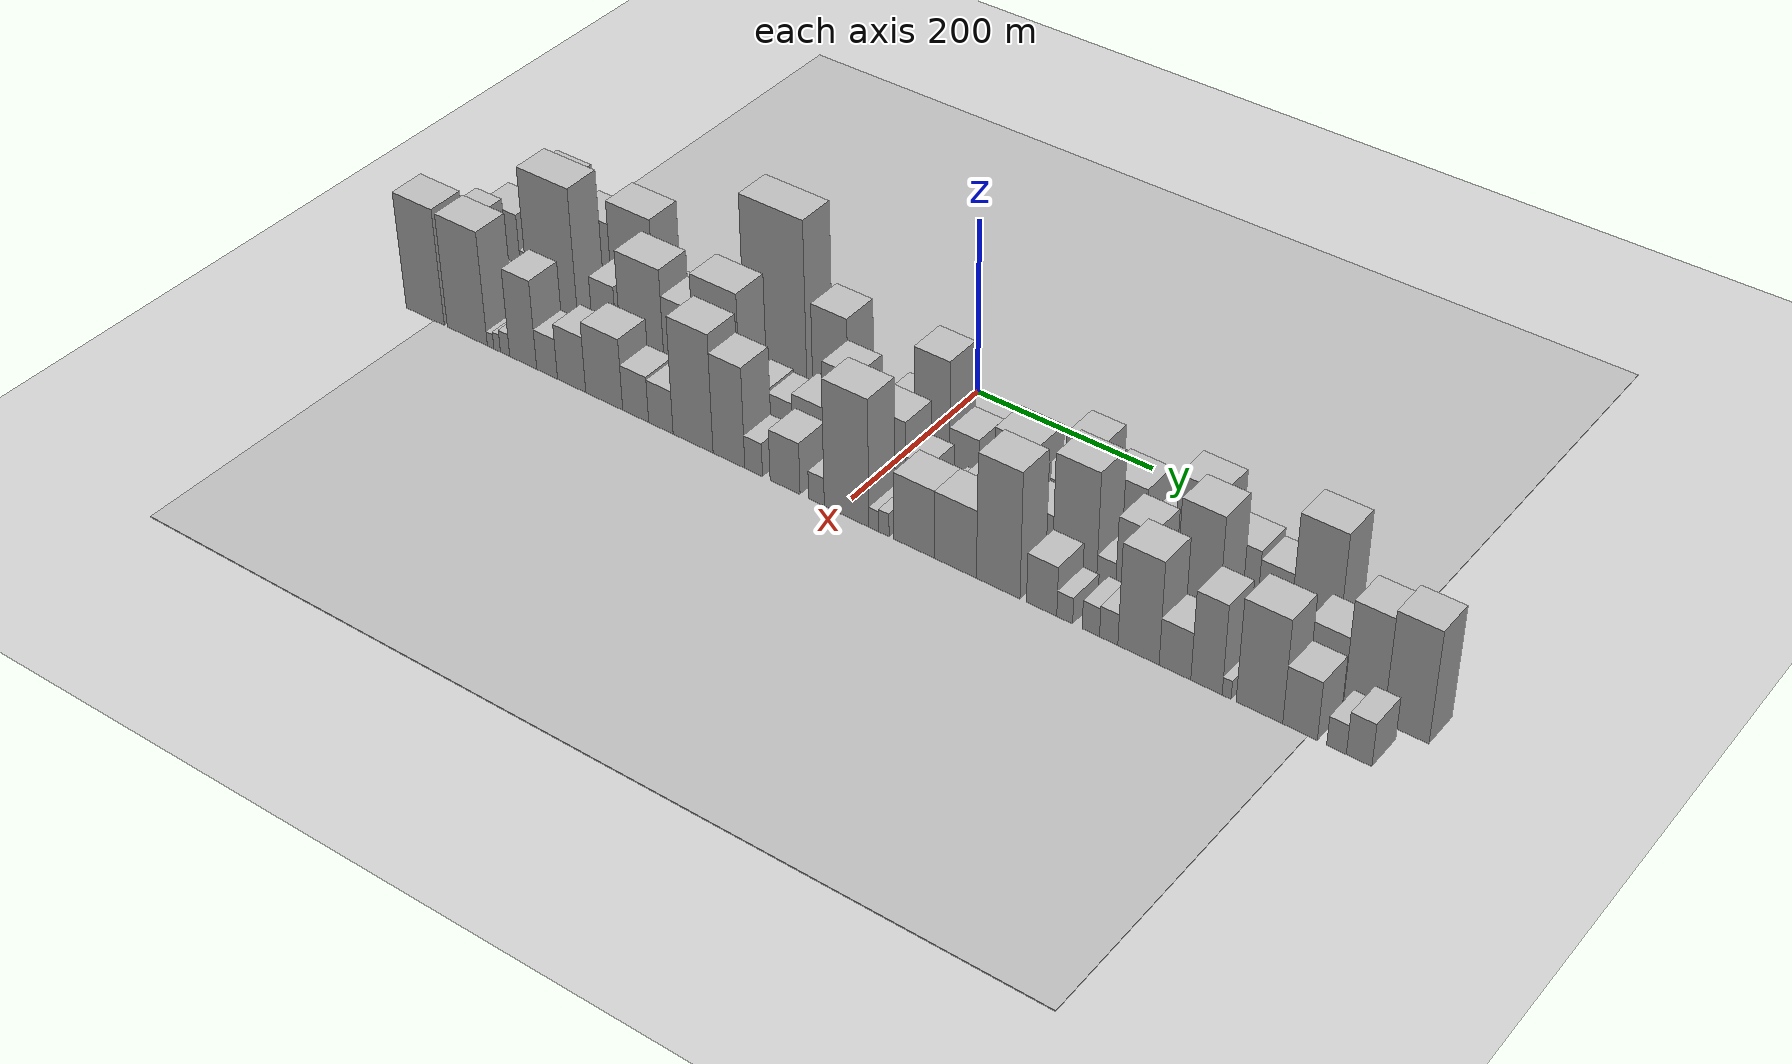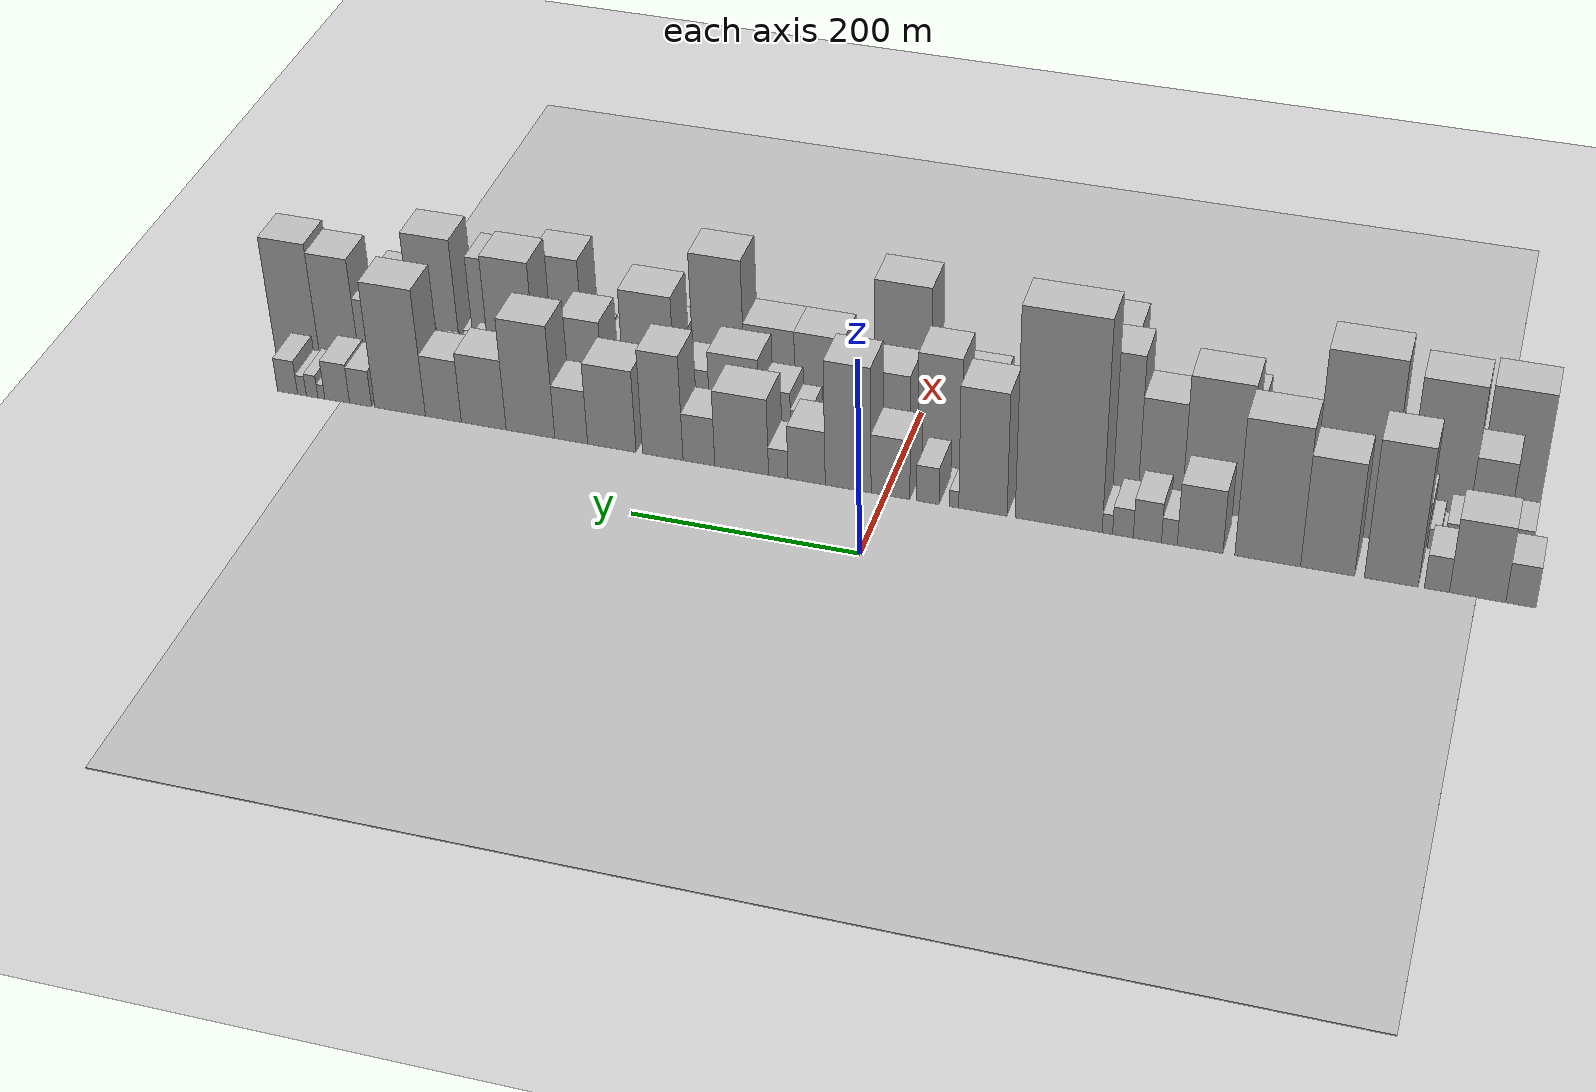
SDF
<?xml version="1.0" encoding="utf-8"?>

<sdf version="1.6">

   <world name="default">

      <gui fullscreen="0">

         <camera name="user_camera">

            <pose>-15 0 4.57585 0 0 0</pose>

            <view_controller>orbit</view_controller>

         </camera>

      </gui>

      <scene>

         <sky>

           <clouds>

             <speed>12</speed>

           </clouds>

         </sky>

         <ambient>0.4 0.4 0.4 1</ambient>

         <background>0.7 0.7 0.7 1</background>

         <shadows>1</shadows>

      </scene>

      <gravity>0 0 -9.8066</gravity>

      <magnetic_field>6e-06 2.3e-05 -4.2e-05</magnetic_field>

      <physics default="0" name="default_physics" type="ode">

         <ode>

            <solver>

               <type>quick</type>

               <iters>10</iters>

               <sor>1.0</sor>

               <use_dynamic_moi_rescaling>0</use_dynamic_moi_rescaling>

            </solver>

            <constraints>

               <cfm>0</cfm>

               <erp>0.2</erp>

               <contact_max_correcting_vel>100</contact_max_correcting_vel>

               <contact_surface_layer>0.001</contact_surface_layer>

            </constraints>

         </ode>

         <max_step_size>0.004</max_step_size>

         <real_time_factor>1</real_time_factor>

         <real_time_update_rate>250</real_time_update_rate>

      </physics>

      <light name="sun" type="directional">

         <cast_shadows>1</cast_shadows>

         <pose>0 0 10 0 0 0</pose>

         <diffuse>0.8 0.8 0.8 1</diffuse>

         <specular>0.2 0.2 0.2 1</specular>

         <attenuation>

            <range>1000</range>

            <constant>0.9</constant>

            <linear>0.01</linear>

            <quadratic>0.001</quadratic>

         </attenuation>

         <direction>-0.5 0.1 -0.9</direction>

      </light>

      <include>

         <name>ground_plane_1</name>

         <uri>model://HANNAS_ground_plane</uri>

         <pose>0 0 0  0 0 0</pose>

      </include>

      <include>

         <name>ground_plane_2</name>

         <uri>model://HANNAS_ground_plane</uri>

         <pose>100 0 0  0 0 0</pose>

      </include>

      <model name="building_1">

         <static>1</static>

         <pose frame="">100.0000 -535.8073 0 0.000000 0.000000 0.000000</pose>

         <link name="link">

            <pose frame="">0 0 21.00 0 0 0</pose>

            <collision name="collision">

               <geometry>

                  <box>

                     <size>40.0000 24.3854 42.0000</size>

                  </box>

               </geometry>

               <max_contacts>10</max_contacts>

               <surface>

                  <contact>

                     <ode/>

                  </contact>

                  <bounce/>

                  <friction>

                     <torsional>

                        <ode/>

                     </torsional>

                     <ode/>

                  </friction>

               </surface>

            </collision>

            <visual name="visual">

               <cast_shadows>0</cast_shadows>

               <geometry>

                  <box>

                     <size>40.0000 24.3854 42.0000</size>

                  </box>

               </geometry>

               <material>

                  <script>

                     <uri>model://HANNAS_wall/materials/scripts</uri>

                     <uri>model://HANNAS_wall/materials/textures</uri>

                     <name>vrc/HANNAS_wall</name>

                  </script>

               </material>

            </visual>

            <self_collide>0</self_collide>

            <enable_wind>0</enable_wind>

            <kinematic>0</kinematic>

         </link>

      </model>

      <model name="building_2">

         <static>1</static>

         <pose frame="">100.0000 -500.7640 0 0.000000 0.000000 0.000000</pose>

         <link name="link">

            <pose frame="">0 0 39.00 0 0 0</pose>

            <collision name="collision">

               <geometry>

                  <box>

                     <size>40.0000 45.7012 78.0000</size>

                  </box>

               </geometry>

               <max_contacts>10</max_contacts>

               <surface>

                  <contact>

                     <ode/>

                  </contact>

                  <bounce/>

                  <friction>

                     <torsional>

                        <ode/>

                     </torsional>

                     <ode/>

                  </friction>

               </surface>

            </collision>

            <visual name="visual">

               <cast_shadows>0</cast_shadows>

               <geometry>

                  <box>

                     <size>40.0000 45.7012 78.0000</size>

                  </box>

               </geometry>

               <material>

                  <script>

                     <uri>model://HANNAS_wall/materials/scripts</uri>

                     <uri>model://HANNAS_wall/materials/textures</uri>

                     <name>vrc/HANNAS_wall</name>

                  </script>

               </material>

            </visual>

            <self_collide>0</self_collide>

            <enable_wind>0</enable_wind>

            <kinematic>0</kinematic>

         </link>

      </model>

      <model name="building_3">

         <static>1</static>

         <pose frame="">100.0000 -467.7036 0 0.000000 0.000000 0.000000</pose>

         <link name="link">

            <pose frame="">0 0 18.00 0 0 0</pose>

            <collision name="collision">

               <geometry>

                  <box>

                     <size>40.0000 20.4196 36.0000</size>

                  </box>

               </geometry>

               <max_contacts>10</max_contacts>

               <surface>

                  <contact>

                     <ode/>

                  </contact>

                  <bounce/>

                  <friction>

                     <torsional>

                        <ode/>

                     </torsional>

                     <ode/>

                  </friction>

               </surface>

            </collision>

            <visual name="visual">

               <cast_shadows>0</cast_shadows>

               <geometry>

                  <box>

                     <size>40.0000 20.4196 36.0000</size>

                  </box>

               </geometry>

               <material>

                  <script>

                     <uri>model://HANNAS_wall/materials/scripts</uri>

                     <uri>model://HANNAS_wall/materials/textures</uri>

                     <name>vrc/HANNAS_wall</name>

                  </script>

               </material>

            </visual>

            <self_collide>0</self_collide>

            <enable_wind>0</enable_wind>

            <kinematic>0</kinematic>

         </link>

      </model>

      <model name="building_4">

         <static>1</static>

         <pose frame="">100.0000 -430.3837 0 0.000000 0.000000 0.000000</pose>

         <link name="link">

            <pose frame="">0 0 72.00 0 0 0</pose>

            <collision name="collision">

               <geometry>

                  <box>

                     <size>40.0000 44.2201 144.0000</size>

                  </box>

               </geometry>

               <max_contacts>10</max_contacts>

               <surface>

                  <contact>

                     <ode/>

                  </contact>

                  <bounce/>

                  <friction>

                     <torsional>

                        <ode/>

                     </torsional>

                     <ode/>

                  </friction>

               </surface>

            </collision>

            <visual name="visual">

               <cast_shadows>0</cast_shadows>

               <geometry>

                  <box>

                     <size>40.0000 44.2201 144.0000</size>

                  </box>

               </geometry>

               <material>

                  <script>

                     <uri>model://HANNAS_wall/materials/scripts</uri>

                     <uri>model://HANNAS_wall/materials/textures</uri>

                     <name>vrc/HANNAS_wall</name>

                  </script>

               </material>

            </visual>

            <self_collide>0</self_collide>

            <enable_wind>0</enable_wind>

            <kinematic>0</kinematic>

         </link>

      </model>

      <model name="building_5">

         <static>1</static>

         <pose frame="">100.0000 -377.8752 0 0.000000 0.000000 0.000000</pose>

         <link name="link">

            <pose frame="">0 0 58.50 0 0 0</pose>

            <collision name="collision">

               <geometry>

                  <box>

                     <size>40.0000 44.7969 117.0000</size>

                  </box>

               </geometry>

               <max_contacts>10</max_contacts>

               <surface>

                  <contact>

                     <ode/>

                  </contact>

                  <bounce/>

                  <friction>

                     <torsional>

                        <ode/>

                     </torsional>

                     <ode/>

                  </friction>

               </surface>

            </collision>

            <visual name="visual">

               <cast_shadows>0</cast_shadows>

               <geometry>

                  <box>

                     <size>40.0000 44.7969 117.0000</size>

                  </box>

               </geometry>

               <material>

                  <script>

                     <uri>model://HANNAS_wall/materials/scripts</uri>

                     <uri>model://HANNAS_wall/materials/textures</uri>

                     <name>vrc/HANNAS_wall</name>

                  </script>

               </material>

            </visual>

            <self_collide>0</self_collide>

            <enable_wind>0</enable_wind>

            <kinematic>0</kinematic>

         </link>

      </model>

      <model name="building_6">

         <static>1</static>

         <pose frame="">100.0000 -328.0431 0 0.000000 0.000000 0.000000</pose>

         <link name="link">

            <pose frame="">0 0 72.00 0 0 0</pose>

            <collision name="collision">

               <geometry>

                  <box>

                     <size>40.0000 54.8673 144.0000</size>

                  </box>

               </geometry>

               <max_contacts>10</max_contacts>

               <surface>

                  <contact>

                     <ode/>

                  </contact>

                  <bounce/>

                  <friction>

                     <torsional>

                        <ode/>

                     </torsional>

                     <ode/>

                  </friction>

               </surface>

            </collision>

            <visual name="visual">

               <cast_shadows>0</cast_shadows>

               <geometry>

                  <box>

                     <size>40.0000 54.8673 144.0000</size>

                  </box>

               </geometry>

               <material>

                  <script>

                     <uri>model://HANNAS_wall/materials/scripts</uri>

                     <uri>model://HANNAS_wall/materials/textures</uri>

                     <name>vrc/HANNAS_wall</name>

                  </script>

               </material>

            </visual>

            <self_collide>0</self_collide>

            <enable_wind>0</enable_wind>

            <kinematic>0</kinematic>

         </link>

      </model>

      <model name="building_7">

         <static>1</static>

         <pose frame="">100.0000 -271.3371 0 0.000000 0.000000 0.000000</pose>

         <link name="link">

            <pose frame="">0 0 33.00 0 0 0</pose>

            <collision name="collision">

               <geometry>

                  <box>

                     <size>40.0000 38.5446 66.0000</size>

                  </box>

               </geometry>

               <max_contacts>10</max_contacts>

               <surface>

                  <contact>

                     <ode/>

                  </contact>

                  <bounce/>

                  <friction>

                     <torsional>

                        <ode/>

                     </torsional>

                     <ode/>

                  </friction>

               </surface>

            </collision>

            <visual name="visual">

               <cast_shadows>0</cast_shadows>

               <geometry>

                  <box>

                     <size>40.0000 38.5446 66.0000</size>

                  </box>

               </geometry>

               <material>

                  <script>

                     <uri>model://HANNAS_wall/materials/scripts</uri>

                     <uri>model://HANNAS_wall/materials/textures</uri>

                     <name>vrc/HANNAS_wall</name>

                  </script>

               </material>

            </visual>

            <self_collide>0</self_collide>

            <enable_wind>0</enable_wind>

            <kinematic>0</kinematic>

         </link>

      </model>

      <model name="building_8">

         <static>1</static>

         <pose frame="">100.0000 -245.4018 0 0.000000 0.000000 0.000000</pose>

         <link name="link">

            <pose frame="">0 0 13.50 0 0 0</pose>

            <collision name="collision">

               <geometry>

                  <box>

                     <size>40.0000 13.3261 27.0000</size>

                  </box>

               </geometry>

               <max_contacts>10</max_contacts>

               <surface>

                  <contact>

                     <ode/>

                  </contact>

                  <bounce/>

                  <friction>

                     <torsional>

                        <ode/>

                     </torsional>

                     <ode/>

                  </friction>

               </surface>

            </collision>

            <visual name="visual">

               <cast_shadows>0</cast_shadows>

               <geometry>

                  <box>

                     <size>40.0000 13.3261 27.0000</size>

                  </box>

               </geometry>

               <material>

                  <script>

                     <uri>model://HANNAS_wall/materials/scripts</uri>

                     <uri>model://HANNAS_wall/materials/textures</uri>

                     <name>vrc/HANNAS_wall</name>

                  </script>

               </material>

            </visual>

            <self_collide>0</self_collide>

            <enable_wind>0</enable_wind>

            <kinematic>0</kinematic>

         </link>

      </model>

      <model name="building_9">

         <static>1</static>

         <pose frame="">100.0000 -226.7744 0 0.000000 0.000000 0.000000</pose>

         <link name="link">

            <pose frame="">0 0 21.00 0 0 0</pose>

            <collision name="collision">

               <geometry>

                  <box>

                     <size>40.0000 23.9287 42.0000</size>

                  </box>

               </geometry>

               <max_contacts>10</max_contacts>

               <surface>

                  <contact>

                     <ode/>

                  </contact>

                  <bounce/>

                  <friction>

                     <torsional>

                        <ode/>

                     </torsional>

                     <ode/>

                  </friction>

               </surface>

            </collision>

            <visual name="visual">

               <cast_shadows>0</cast_shadows>

               <geometry>

                  <box>

                     <size>40.0000 23.9287 42.0000</size>

                  </box>

               </geometry>

               <material>

                  <script>

                     <uri>model://HANNAS_wall/materials/scripts</uri>

                     <uri>model://HANNAS_wall/materials/textures</uri>

                     <name>vrc/HANNAS_wall</name>

                  </script>

               </material>

            </visual>

            <self_collide>0</self_collide>

            <enable_wind>0</enable_wind>

            <kinematic>0</kinematic>

         </link>

      </model>

      <model name="building_10">

         <static>1</static>

         <pose frame="">100.0000 -205.9843 0 0.000000 0.000000 0.000000</pose>

         <link name="link">

            <pose frame="">0 0 15.00 0 0 0</pose>

            <collision name="collision">

               <geometry>

                  <box>

                     <size>40.0000 17.6515 30.0000</size>

                  </box>

               </geometry>

               <max_contacts>10</max_contacts>

               <surface>

                  <contact>

                     <ode/>

                  </contact>

                  <bounce/>

                  <friction>

                     <torsional>

                        <ode/>

                     </torsional>

                     <ode/>

                  </friction>

               </surface>

            </collision>

            <visual name="visual">

               <cast_shadows>0</cast_shadows>

               <geometry>

                  <box>

                     <size>40.0000 17.6515 30.0000</size>

                  </box>

               </geometry>

               <material>

                  <script>

                     <uri>model://HANNAS_wall/materials/scripts</uri>

                     <uri>model://HANNAS_wall/materials/textures</uri>

                     <name>vrc/HANNAS_wall</name>

                  </script>

               </material>

            </visual>

            <self_collide>0</self_collide>

            <enable_wind>0</enable_wind>

            <kinematic>0</kinematic>

         </link>

      </model>

      <model name="building_11">

         <static>1</static>

         <pose frame="">100.0000 -192.7051 0 0.000000 0.000000 0.000000</pose>

         <link name="link">

            <pose frame="">0 0 10.50 0 0 0</pose>

            <collision name="collision">

               <geometry>

                  <box>

                     <size>40.0000 8.9070 21.0000</size>

                  </box>

               </geometry>

               <max_contacts>10</max_contacts>

               <surface>

                  <contact>

                     <ode/>

                  </contact>

                  <bounce/>

                  <friction>

                     <torsional>

                        <ode/>

                     </torsional>

                     <ode/>

                  </friction>

               </surface>

            </collision>

            <visual name="visual">

               <cast_shadows>0</cast_shadows>

               <geometry>

                  <box>

                     <size>40.0000 8.9070 21.0000</size>

                  </box>

               </geometry>

               <material>

                  <script>

                     <uri>model://HANNAS_wall/materials/scripts</uri>

                     <uri>model://HANNAS_wall/materials/textures</uri>

                     <name>vrc/HANNAS_wall</name>

                  </script>

               </material>

            </visual>

            <self_collide>0</self_collide>

            <enable_wind>0</enable_wind>

            <kinematic>0</kinematic>

         </link>

      </model>

      <model name="building_12">

         <static>1</static>

         <pose frame="">100.0000 -150.8163 0 0.000000 0.000000 0.000000</pose>

         <link name="link">

            <pose frame="">0 0 109.50 0 0 0</pose>

            <collision name="collision">

               <geometry>

                  <box>

                     <size>40.0000 74.8706 219.0000</size>

                  </box>

               </geometry>

               <max_contacts>10</max_contacts>

               <surface>

                  <contact>

                     <ode/>

                  </contact>

                  <bounce/>

                  <friction>

                     <torsional>

                        <ode/>

                     </torsional>

                     <ode/>

                  </friction>

               </surface>

            </collision>

            <visual name="visual">

               <cast_shadows>0</cast_shadows>

               <geometry>

                  <box>

                     <size>40.0000 74.8706 219.0000</size>

                  </box>

               </geometry>

               <material>

                  <script>

                     <uri>model://HANNAS_wall/materials/scripts</uri>

                     <uri>model://HANNAS_wall/materials/textures</uri>

                     <name>vrc/HANNAS_wall</name>

                  </script>

               </material>

            </visual>

            <self_collide>0</self_collide>

            <enable_wind>0</enable_wind>

            <kinematic>0</kinematic>

         </link>

      </model>

      <model name="building_13">

         <static>1</static>

         <pose frame="">100.0000 -85.3873 0 0.000000 0.000000 0.000000</pose>

         <link name="link">

            <pose frame="">0 0 64.50 0 0 0</pose>

            <collision name="collision">

               <geometry>

                  <box>

                     <size>40.0000 41.9874 129.0000</size>

                  </box>

               </geometry>

               <max_contacts>10</max_contacts>

               <surface>

                  <contact>

                     <ode/>

                  </contact>

                  <bounce/>

                  <friction>

                     <torsional>

                        <ode/>

                     </torsional>

                     <ode/>

                  </friction>

               </surface>

            </collision>

            <visual name="visual">

               <cast_shadows>0</cast_shadows>

               <geometry>

                  <box>

                     <size>40.0000 41.9874 129.0000</size>

                  </box>

               </geometry>

               <material>

                  <script>

                     <uri>model://HANNAS_wall/materials/scripts</uri>

                     <uri>model://HANNAS_wall/materials/textures</uri>

                     <name>vrc/HANNAS_wall</name>

                  </script>

               </material>

            </visual>

            <self_collide>0</self_collide>

            <enable_wind>0</enable_wind>

            <kinematic>0</kinematic>

         </link>

      </model>

      <model name="building_14">

         <static>1</static>

         <pose frame="">100.0000 -60.3403 0 0.000000 0.000000 0.000000</pose>

         <link name="link">

            <pose frame="">0 0 9.00 0 0 0</pose>

            <collision name="collision">

               <geometry>

                  <box>

                     <size>40.0000 8.1066 18.0000</size>

                  </box>

               </geometry>

               <max_contacts>10</max_contacts>

               <surface>

                  <contact>

                     <ode/>

                  </contact>

                  <bounce/>

                  <friction>

                     <torsional>

                        <ode/>

                     </torsional>

                     <ode/>

                  </friction>

               </surface>

            </collision>

            <visual name="visual">

               <cast_shadows>0</cast_shadows>

               <geometry>

                  <box>

                     <size>40.0000 8.1066 18.0000</size>

                  </box>

               </geometry>

               <material>

                  <script>

                     <uri>model://HANNAS_wall/materials/scripts</uri>

                     <uri>model://HANNAS_wall/materials/textures</uri>

                     <name>vrc/HANNAS_wall</name>

                  </script>

               </material>

            </visual>

            <self_collide>0</self_collide>

            <enable_wind>0</enable_wind>

            <kinematic>0</kinematic>

         </link>

      </model>

      <model name="building_15">

         <static>1</static>

         <pose frame="">100.0000 -37.4372 0 0.000000 0.000000 0.000000</pose>

         <link name="link">

            <pose frame="">0 0 19.50 0 0 0</pose>

            <collision name="collision">

               <geometry>

                  <box>

                     <size>40.0000 19.6997 39.0000</size>

                  </box>

               </geometry>

               <max_contacts>10</max_contacts>

               <surface>

                  <contact>

                     <ode/>

                  </contact>

                  <bounce/>

                  <friction>

                     <torsional>

                        <ode/>

                     </torsional>

                     <ode/>

                  </friction>

               </surface>

            </collision>

            <visual name="visual">

               <cast_shadows>0</cast_shadows>

               <geometry>

                  <box>

                     <size>40.0000 19.6997 39.0000</size>

                  </box>

               </geometry>

               <material>

                  <script>

                     <uri>model://HANNAS_wall/materials/scripts</uri>

                     <uri>model://HANNAS_wall/materials/textures</uri>

                     <name>vrc/HANNAS_wall</name>

                  </script>

               </material>

            </visual>

            <self_collide>0</self_collide>

            <enable_wind>0</enable_wind>

            <kinematic>0</kinematic>

         </link>

      </model>

      <model name="building_16">

         <static>1</static>

         <pose frame="">100.0000 -4.4904 0 0.000000 0.000000 0.000000</pose>

         <link name="link">

            <pose frame="">0 0 31.50 0 0 0</pose>

            <collision name="collision">

               <geometry>

                  <box>

                     <size>40.0000 34.1938 63.0000</size>

                  </box>

               </geometry>

               <max_contacts>10</max_contacts>

               <surface>

                  <contact>

                     <ode/>

                  </contact>

                  <bounce/>

                  <friction>

                     <torsional>

                        <ode/>

                     </torsional>

                     <ode/>

                  </friction>

               </surface>

            </collision>

            <visual name="visual">

               <cast_shadows>0</cast_shadows>

               <geometry>

                  <box>

                     <size>40.0000 34.1938 63.0000</size>

                  </box>

               </geometry>

               <material>

                  <script>

                     <uri>model://HANNAS_wall/materials/scripts</uri>

                     <uri>model://HANNAS_wall/materials/textures</uri>

                     <name>vrc/HANNAS_wall</name>

                  </script>

               </material>

            </visual>

            <self_collide>0</self_collide>

            <enable_wind>0</enable_wind>

            <kinematic>0</kinematic>

         </link>

      </model>

      <model name="building_17">

         <static>1</static>

         <pose frame="">100.0000 32.9341 0 0.000000 0.000000 0.000000</pose>

         <link name="link">

            <pose frame="">0 0 66.00 0 0 0</pose>

            <collision name="collision">

               <geometry>

                  <box>

                     <size>40.0000 40.6553 132.0000</size>

                  </box>

               </geometry>

               <max_contacts>10</max_contacts>

               <surface>

                  <contact>

                     <ode/>

                  </contact>

                  <bounce/>

                  <friction>

                     <torsional>

                        <ode/>

                     </torsional>

                     <ode/>

                  </friction>

               </surface>

            </collision>

            <visual name="visual">

               <cast_shadows>0</cast_shadows>

               <geometry>

                  <box>

                     <size>40.0000 40.6553 132.0000</size>

                  </box>

               </geometry>

               <material>

                  <script>

                     <uri>model://HANNAS_wall/materials/scripts</uri>

                     <uri>model://HANNAS_wall/materials/textures</uri>

                     <name>vrc/HANNAS_wall</name>

                  </script>

               </material>

            </visual>

            <self_collide>0</self_collide>

            <enable_wind>0</enable_wind>

            <kinematic>0</kinematic>

         </link>

      </model>

      <model name="building_18">

         <static>1</static>

         <pose frame="">100.0000 69.8813 0 0.000000 0.000000 0.000000</pose>

         <link name="link">

            <pose frame="">0 0 28.50 0 0 0</pose>

            <collision name="collision">

               <geometry>

                  <box>

                     <size>40.0000 33.2389 57.0000</size>

                  </box>

               </geometry>

               <max_contacts>10</max_contacts>

               <surface>

                  <contact>

                     <ode/>

                  </contact>

                  <bounce/>

                  <friction>

                     <torsional>

                        <ode/>

                     </torsional>

                     <ode/>

                  </friction>

               </surface>

            </collision>

            <visual name="visual">

               <cast_shadows>0</cast_shadows>

               <geometry>

                  <box>

                     <size>40.0000 33.2389 57.0000</size>

                  </box>

               </geometry>

               <material>

                  <script>

                     <uri>model://HANNAS_wall/materials/scripts</uri>

                     <uri>model://HANNAS_wall/materials/textures</uri>

                     <name>vrc/HANNAS_wall</name>

                  </script>

               </material>

            </visual>

            <self_collide>0</self_collide>

            <enable_wind>0</enable_wind>

            <kinematic>0</kinematic>

         </link>

      </model>

      <model name="building_19">

         <static>1</static>

         <pose frame="">100.0000 95.2057 0 0.000000 0.000000 0.000000</pose>

         <link name="link">

            <pose frame="">0 0 15.00 0 0 0</pose>

            <collision name="collision">

               <geometry>

                  <box>

                     <size>40.0000 17.4098 30.0000</size>

                  </box>

               </geometry>

               <max_contacts>10</max_contacts>

               <surface>

                  <contact>

                     <ode/>

                  </contact>

                  <bounce/>

                  <friction>

                     <torsional>

                        <ode/>

                     </torsional>

                     <ode/>

                  </friction>

               </surface>

            </collision>

            <visual name="visual">

               <cast_shadows>0</cast_shadows>

               <geometry>

                  <box>

                     <size>40.0000 17.4098 30.0000</size>

                  </box>

               </geometry>

               <material>

                  <script>

                     <uri>model://HANNAS_wall/materials/scripts</uri>

                     <uri>model://HANNAS_wall/materials/textures</uri>

                     <name>vrc/HANNAS_wall</name>

                  </script>

               </material>

            </visual>

            <self_collide>0</self_collide>

            <enable_wind>0</enable_wind>

            <kinematic>0</kinematic>

         </link>

      </model>

      <model name="building_20">

         <static>1</static>

         <pose frame="">100.0000 128.1146 0 0.000000 0.000000 0.000000</pose>

         <link name="link">

            <pose frame="">0 0 40.50 0 0 0</pose>

            <collision name="collision">

               <geometry>

                  <box>

                     <size>40.0000 48.4081 81.0000</size>

                  </box>

               </geometry>

               <max_contacts>10</max_contacts>

               <surface>

                  <contact>

                     <ode/>

                  </contact>

                  <bounce/>

                  <friction>

                     <torsional>

                        <ode/>

                     </torsional>

                     <ode/>

                  </friction>

               </surface>

            </collision>

            <visual name="visual">

               <cast_shadows>0</cast_shadows>

               <geometry>

                  <box>

                     <size>40.0000 48.4081 81.0000</size>

                  </box>

               </geometry>

               <material>

                  <script>

                     <uri>model://HANNAS_wall/materials/scripts</uri>

                     <uri>model://HANNAS_wall/materials/textures</uri>

                     <name>vrc/HANNAS_wall</name>

                  </script>

               </material>

            </visual>

            <self_collide>0</self_collide>

            <enable_wind>0</enable_wind>

            <kinematic>0</kinematic>

         </link>

      </model>

      <model name="building_21">

         <static>1</static>

         <pose frame="">100.0000 166.6910 0 0.000000 0.000000 0.000000</pose>

         <link name="link">

            <pose frame="">0 0 25.50 0 0 0</pose>

            <collision name="collision">

               <geometry>

                  <box>

                     <size>40.0000 28.7448 51.0000</size>

                  </box>

               </geometry>

               <max_contacts>10</max_contacts>

               <surface>

                  <contact>

                     <ode/>

                  </contact>

                  <bounce/>

                  <friction>

                     <torsional>

                        <ode/>

                     </torsional>

                     <ode/>

                  </friction>

               </surface>

            </collision>

            <visual name="visual">

               <cast_shadows>0</cast_shadows>

               <geometry>

                  <box>

                     <size>40.0000 28.7448 51.0000</size>

                  </box>

               </geometry>

               <material>

                  <script>

                     <uri>model://HANNAS_wall/materials/scripts</uri>

                     <uri>model://HANNAS_wall/materials/textures</uri>

                     <name>vrc/HANNAS_wall</name>

                  </script>

               </material>

            </visual>

            <self_collide>0</self_collide>

            <enable_wind>0</enable_wind>

            <kinematic>0</kinematic>

         </link>

      </model>

      <model name="building_22">

         <static>1</static>

         <pose frame="">100.0000 199.5196 0 0.000000 0.000000 0.000000</pose>

         <link name="link">

            <pose frame="">0 0 55.50 0 0 0</pose>

            <collision name="collision">

               <geometry>

                  <box>

                     <size>40.0000 36.9123 111.0000</size>

                  </box>

               </geometry>

               <max_contacts>10</max_contacts>

               <surface>

                  <contact>

                     <ode/>

                  </contact>

                  <bounce/>

                  <friction>

                     <torsional>

                        <ode/>

                     </torsional>

                     <ode/>

                  </friction>

               </surface>

            </collision>

            <visual name="visual">

               <cast_shadows>0</cast_shadows>

               <geometry>

                  <box>

                     <size>40.0000 36.9123 111.0000</size>

                  </box>

               </geometry>

               <material>

                  <script>

                     <uri>model://HANNAS_wall/materials/scripts</uri>

                     <uri>model://HANNAS_wall/materials/textures</uri>

                     <name>vrc/HANNAS_wall</name>

                  </script>

               </material>

            </visual>

            <self_collide>0</self_collide>

            <enable_wind>0</enable_wind>

            <kinematic>0</kinematic>

         </link>

      </model>

      <model name="building_23">

         <static>1</static>

         <pose frame="">100.0000 246.2074 0 0.000000 0.000000 0.000000</pose>

         <link name="link">

            <pose frame="">0 0 43.50 0 0 0</pose>

            <collision name="collision">

               <geometry>

                  <box>

                     <size>40.0000 44.4633 87.0000</size>

                  </box>

               </geometry>

               <max_contacts>10</max_contacts>

               <surface>

                  <contact>

                     <ode/>

                  </contact>

                  <bounce/>

                  <friction>

                     <torsional>

                        <ode/>

                     </torsional>

                     <ode/>

                  </friction>

               </surface>

            </collision>

            <visual name="visual">

               <cast_shadows>0</cast_shadows>

               <geometry>

                  <box>

                     <size>40.0000 44.4633 87.0000</size>

                  </box>

               </geometry>

               <material>

                  <script>

                     <uri>model://HANNAS_wall/materials/scripts</uri>

                     <uri>model://HANNAS_wall/materials/textures</uri>

                     <name>vrc/HANNAS_wall</name>

                  </script>

               </material>

            </visual>

            <self_collide>0</self_collide>

            <enable_wind>0</enable_wind>

            <kinematic>0</kinematic>

         </link>

      </model>

      <model name="building_24">

         <static>1</static>

         <pose frame="">100.0000 283.5786 0 0.000000 0.000000 0.000000</pose>

         <link name="link">

            <pose frame="">0 0 28.50 0 0 0</pose>

            <collision name="collision">

               <geometry>

                  <box>

                     <size>40.0000 30.2793 57.0000</size>

                  </box>

               </geometry>

               <max_contacts>10</max_contacts>

               <surface>

                  <contact>

                     <ode/>

                  </contact>

                  <bounce/>

                  <friction>

                     <torsional>

                        <ode/>

                     </torsional>

                     <ode/>

                  </friction>

               </surface>

            </collision>

            <visual name="visual">

               <cast_shadows>0</cast_shadows>

               <geometry>

                  <box>

                     <size>40.0000 30.2793 57.0000</size>

                  </box>

               </geometry>

               <material>

                  <script>

                     <uri>model://HANNAS_wall/materials/scripts</uri>

                     <uri>model://HANNAS_wall/materials/textures</uri>

                     <name>vrc/HANNAS_wall</name>

                  </script>

               </material>

            </visual>

            <self_collide>0</self_collide>

            <enable_wind>0</enable_wind>

            <kinematic>0</kinematic>

         </link>

      </model>

      <model name="building_25">

         <static>1</static>

         <pose frame="">100.0000 321.3481 0 0.000000 0.000000 0.000000</pose>

         <link name="link">

            <pose frame="">0 0 60.00 0 0 0</pose>

            <collision name="collision">

               <geometry>

                  <box>

                     <size>40.0000 45.2596 120.0000</size>

                  </box>

               </geometry>

               <max_contacts>10</max_contacts>

               <surface>

                  <contact>

                     <ode/>

                  </contact>

                  <bounce/>

                  <friction>

                     <torsional>

                        <ode/>

                     </torsional>

                     <ode/>

                  </friction>

               </surface>

            </collision>

            <visual name="visual">

               <cast_shadows>0</cast_shadows>

               <geometry>

                  <box>

                     <size>40.0000 45.2596 120.0000</size>

                  </box>

               </geometry>

               <material>

                  <script>

                     <uri>model://HANNAS_wall/materials/scripts</uri>

                     <uri>model://HANNAS_wall/materials/textures</uri>

                     <name>vrc/HANNAS_wall</name>

                  </script>

               </material>

            </visual>

            <self_collide>0</self_collide>

            <enable_wind>0</enable_wind>

            <kinematic>0</kinematic>

         </link>

      </model>

      <model name="building_26">

         <static>1</static>

         <pose frame="">100.0000 364.9645 0 0.000000 0.000000 0.000000</pose>

         <link name="link">

            <pose frame="">0 0 37.50 0 0 0</pose>

            <collision name="collision">

               <geometry>

                  <box>

                     <size>40.0000 41.9731 75.0000</size>

                  </box>

               </geometry>

               <max_contacts>10</max_contacts>

               <surface>

                  <contact>

                     <ode/>

                  </contact>

                  <bounce/>

                  <friction>

                     <torsional>

                        <ode/>

                     </torsional>

                     <ode/>

                  </friction>

               </surface>

            </collision>

            <visual name="visual">

               <cast_shadows>0</cast_shadows>

               <geometry>

                  <box>

                     <size>40.0000 41.9731 75.0000</size>

                  </box>

               </geometry>

               <material>

                  <script>

                     <uri>model://HANNAS_wall/materials/scripts</uri>

                     <uri>model://HANNAS_wall/materials/textures</uri>

                     <name>vrc/HANNAS_wall</name>

                  </script>

               </material>

            </visual>

            <self_collide>0</self_collide>

            <enable_wind>0</enable_wind>

            <kinematic>0</kinematic>

         </link>

      </model>

      <model name="building_27">

         <static>1</static>

         <pose frame="">100.0000 402.8647 0 0.000000 0.000000 0.000000</pose>

         <link name="link">

            <pose frame="">0 0 33.00 0 0 0</pose>

            <collision name="collision">

               <geometry>

                  <box>

                     <size>40.0000 33.8273 66.0000</size>

                  </box>

               </geometry>

               <max_contacts>10</max_contacts>

               <surface>

                  <contact>

                     <ode/>

                  </contact>

                  <bounce/>

                  <friction>

                     <torsional>

                        <ode/>

                     </torsional>

                     <ode/>

                  </friction>

               </surface>

            </collision>

            <visual name="visual">

               <cast_shadows>0</cast_shadows>

               <geometry>

                  <box>

                     <size>40.0000 33.8273 66.0000</size>

                  </box>

               </geometry>

               <material>

                  <script>

                     <uri>model://HANNAS_wall/materials/scripts</uri>

                     <uri>model://HANNAS_wall/materials/textures</uri>

                     <name>vrc/HANNAS_wall</name>

                  </script>

               </material>

            </visual>

            <self_collide>0</self_collide>

            <enable_wind>0</enable_wind>

            <kinematic>0</kinematic>

         </link>

      </model>

      <model name="building_28">

         <static>1</static>

         <pose frame="">100.0000 443.7735 0 0.000000 0.000000 0.000000</pose>

         <link name="link">

            <pose frame="">0 0 67.50 0 0 0</pose>

            <collision name="collision">

               <geometry>

                  <box>

                     <size>40.0000 47.9902 135.0000</size>

                  </box>

               </geometry>

               <max_contacts>10</max_contacts>

               <surface>

                  <contact>

                     <ode/>

                  </contact>

                  <bounce/>

                  <friction>

                     <torsional>

                        <ode/>

                     </torsional>

                     <ode/>

                  </friction>

               </surface>

            </collision>

            <visual name="visual">

               <cast_shadows>0</cast_shadows>

               <geometry>

                  <box>

                     <size>40.0000 47.9902 135.0000</size>

                  </box>

               </geometry>

               <material>

                  <script>

                     <uri>model://HANNAS_wall/materials/scripts</uri>

                     <uri>model://HANNAS_wall/materials/textures</uri>

                     <name>vrc/HANNAS_wall</name>

                  </script>

               </material>

            </visual>

            <self_collide>0</self_collide>

            <enable_wind>0</enable_wind>

            <kinematic>0</kinematic>

         </link>

      </model>

      <model name="building_29">

         <static>1</static>

         <pose frame="">100.0000 481.3211 0 0.000000 0.000000 0.000000</pose>

         <link name="link">

            <pose frame="">0 0 19.50 0 0 0</pose>

            <collision name="collision">

               <geometry>

                  <box>

                     <size>40.0000 21.1052 39.0000</size>

                  </box>

               </geometry>

               <max_contacts>10</max_contacts>

               <surface>

                  <contact>

                     <ode/>

                  </contact>

                  <bounce/>

                  <friction>

                     <torsional>

                        <ode/>

                     </torsional>

                     <ode/>

                  </friction>

               </surface>

            </collision>

            <visual name="visual">

               <cast_shadows>0</cast_shadows>

               <geometry>

                  <box>

                     <size>40.0000 21.1052 39.0000</size>

                  </box>

               </geometry>

               <material>

                  <script>

                     <uri>model://HANNAS_wall/materials/scripts</uri>

                     <uri>model://HANNAS_wall/materials/textures</uri>

                     <name>vrc/HANNAS_wall</name>

                  </script>

               </material>

            </visual>

            <self_collide>0</self_collide>

            <enable_wind>0</enable_wind>

            <kinematic>0</kinematic>

         </link>

      </model>

      <model name="building_30">

         <static>1</static>

         <pose frame="">100.0000 503.7312 0 0.000000 0.000000 0.000000</pose>

         <link name="link">

            <pose frame="">0 0 21.00 0 0 0</pose>

            <collision name="collision">

               <geometry>

                  <box>

                     <size>40.0000 23.7150 42.0000</size>

                  </box>

               </geometry>

               <max_contacts>10</max_contacts>

               <surface>

                  <contact>

                     <ode/>

                  </contact>

                  <bounce/>

                  <friction>

                     <torsional>

                        <ode/>

                     </torsional>

                     <ode/>

                  </friction>

               </surface>

            </collision>

            <visual name="visual">

               <cast_shadows>0</cast_shadows>

               <geometry>

                  <box>

                     <size>40.0000 23.7150 42.0000</size>

                  </box>

               </geometry>

               <material>

                  <script>

                     <uri>model://HANNAS_wall/materials/scripts</uri>

                     <uri>model://HANNAS_wall/materials/textures</uri>

                     <name>vrc/HANNAS_wall</name>

                  </script>

               </material>

            </visual>

            <self_collide>0</self_collide>

            <enable_wind>0</enable_wind>

            <kinematic>0</kinematic>

         </link>

      </model>

      <model name="building_31">

         <static>1</static>

         <pose frame="">100.0000 518.9350 0 0.000000 0.000000 0.000000</pose>

         <link name="link">

            <pose frame="">0 0 7.50 0 0 0</pose>

            <collision name="collision">

               <geometry>

                  <box>

                     <size>40.0000 6.6925 15.0000</size>

                  </box>

               </geometry>

               <max_contacts>10</max_contacts>

               <surface>

                  <contact>

                     <ode/>

                  </contact>

                  <bounce/>

                  <friction>

                     <torsional>

                        <ode/>

                     </torsional>

                     <ode/>

                  </friction>

               </surface>

            </collision>

            <visual name="visual">

               <cast_shadows>0</cast_shadows>

               <geometry>

                  <box>

                     <size>40.0000 6.6925 15.0000</size>

                  </box>

               </geometry>

               <material>

                  <script>

                     <uri>model://HANNAS_wall/materials/scripts</uri>

                     <uri>model://HANNAS_wall/materials/textures</uri>

                     <name>vrc/HANNAS_wall</name>

                  </script>

               </material>

            </visual>

            <self_collide>0</self_collide>

            <enable_wind>0</enable_wind>

            <kinematic>0</kinematic>

         </link>

      </model>

      <model name="building_32">

         <static>1</static>

         <pose frame="">100.0000 527.8249 0 0.000000 0.000000 0.000000</pose>

         <link name="link">

            <pose frame="">0 0 12.00 0 0 0</pose>

            <collision name="collision">

               <geometry>

                  <box>

                     <size>40.0000 11.0874 24.0000</size>

                  </box>

               </geometry>

               <max_contacts>10</max_contacts>

               <surface>

                  <contact>

                     <ode/>

                  </contact>

                  <bounce/>

                  <friction>

                     <torsional>

                        <ode/>

                     </torsional>

                     <ode/>

                  </friction>

               </surface>

            </collision>

            <visual name="visual">

               <cast_shadows>0</cast_shadows>

               <geometry>

                  <box>

                     <size>40.0000 11.0874 24.0000</size>

                  </box>

               </geometry>

               <material>

                  <script>

                     <uri>model://HANNAS_wall/materials/scripts</uri>

                     <uri>model://HANNAS_wall/materials/textures</uri>

                     <name>vrc/HANNAS_wall</name>

                  </script>

               </material>

            </visual>

            <self_collide>0</self_collide>

            <enable_wind>0</enable_wind>

            <kinematic>0</kinematic>

         </link>

      </model>

      <model name="building_33">

         <static>1</static>

         <pose frame="">100.0000 537.5927 0 0.000000 0.000000 0.000000</pose>

         <link name="link">

            <pose frame="">0 0 10.50 0 0 0</pose>

            <collision name="collision">

               <geometry>

                  <box>

                     <size>40.0000 8.4481 21.0000</size>

                  </box>

               </geometry>

               <max_contacts>10</max_contacts>

               <surface>

                  <contact>

                     <ode/>

                  </contact>

                  <bounce/>

                  <friction>

                     <torsional>

                        <ode/>

                     </torsional>

                     <ode/>

                  </friction>

               </surface>

            </collision>

            <visual name="visual">

               <cast_shadows>0</cast_shadows>

               <geometry>

                  <box>

                     <size>40.0000 8.4481 21.0000</size>

                  </box>

               </geometry>

               <material>

                  <script>

                     <uri>model://HANNAS_wall/materials/scripts</uri>

                     <uri>model://HANNAS_wall/materials/textures</uri>

                     <name>vrc/HANNAS_wall</name>

                  </script>

               </material>

            </visual>

            <self_collide>0</self_collide>

            <enable_wind>0</enable_wind>

            <kinematic>0</kinematic>

         </link>

      </model>

      <model name="building_34">

         <static>1</static>

         <pose frame="">100.0000 551.4282 0 0.000000 0.000000 0.000000</pose>

         <link name="link">

            <pose frame="">0 0 18.00 0 0 0</pose>

            <collision name="collision">

               <geometry>

                  <box>

                     <size>40.0000 19.2229 36.0000</size>

                  </box>

               </geometry>

               <max_contacts>10</max_contacts>

               <surface>

                  <contact>

                     <ode/>

                  </contact>

                  <bounce/>

                  <friction>

                     <torsional>

                        <ode/>

                     </torsional>

                     <ode/>

                  </friction>

               </surface>

            </collision>

            <visual name="visual">

               <cast_shadows>0</cast_shadows>

               <geometry>

                  <box>

                     <size>40.0000 19.2229 36.0000</size>

                  </box>

               </geometry>

               <material>

                  <script>

                     <uri>model://HANNAS_wall/materials/scripts</uri>

                     <uri>model://HANNAS_wall/materials/textures</uri>

                     <name>vrc/HANNAS_wall</name>

                  </script>

               </material>

            </visual>

            <self_collide>0</self_collide>

            <enable_wind>0</enable_wind>

            <kinematic>0</kinematic>

         </link>

      </model>

      <model name="building_35">

         <static>1</static>

         <pose frame="">152.0000 -527.2593 0 0.000000 0.000000 0.000000</pose>

         <link name="link">

            <pose frame="">0 0 18.00 0 0 0</pose>

            <collision name="collision">

               <geometry>

                  <box>

                     <size>40.0000 21.4814 36.0000</size>

                  </box>

               </geometry>

               <max_contacts>10</max_contacts>

               <surface>

                  <contact>

                     <ode/>

                  </contact>

                  <bounce/>

                  <friction>

                     <torsional>

                        <ode/>

                     </torsional>

                     <ode/>

                  </friction>

               </surface>

            </collision>

            <visual name="visual">

               <cast_shadows>0</cast_shadows>

               <geometry>

                  <box>

                     <size>40.0000 21.4814 36.0000</size>

                  </box>

               </geometry>

               <material>

                  <script>

                     <uri>model://HANNAS_wall/materials/scripts</uri>

                     <uri>model://HANNAS_wall/materials/textures</uri>

                     <name>vrc/HANNAS_wall</name>

                  </script>

               </material>

            </visual>

            <self_collide>0</self_collide>

            <enable_wind>0</enable_wind>

            <kinematic>0</kinematic>

         </link>

      </model>

      <model name="building_36">

         <static>1</static>

         <pose frame="">152.0000 -499.8316 0 0.000000 0.000000 0.000000</pose>

         <link name="link">

            <pose frame="">0 0 51.00 0 0 0</pose>

            <collision name="collision">

               <geometry>

                  <box>

                     <size>40.0000 33.3740 102.0000</size>

                  </box>

               </geometry>

               <max_contacts>10</max_contacts>

               <surface>

                  <contact>

                     <ode/>

                  </contact>

                  <bounce/>

                  <friction>

                     <torsional>

                        <ode/>

                     </torsional>

                     <ode/>

                  </friction>

               </surface>

            </collision>

            <visual name="visual">

               <cast_shadows>0</cast_shadows>

               <geometry>

                  <box>

                     <size>40.0000 33.3740 102.0000</size>

                  </box>

               </geometry>

               <material>

                  <script>

                     <uri>model://HANNAS_wall/materials/scripts</uri>

                     <uri>model://HANNAS_wall/materials/textures</uri>

                     <name>vrc/HANNAS_wall</name>

                  </script>

               </material>

            </visual>

            <self_collide>0</self_collide>

            <enable_wind>0</enable_wind>

            <kinematic>0</kinematic>

         </link>

      </model>

      <model name="building_37">

         <static>1</static>

         <pose frame="">152.0000 -474.8939 0 0.000000 0.000000 0.000000</pose>

         <link name="link">

            <pose frame="">0 0 15.00 0 0 0</pose>

            <collision name="collision">

               <geometry>

                  <box>

                     <size>40.0000 16.5013 30.0000</size>

                  </box>

               </geometry>

               <max_contacts>10</max_contacts>

               <surface>

                  <contact>

                     <ode/>

                  </contact>

                  <bounce/>

                  <friction>

                     <torsional>

                        <ode/>

                     </torsional>

                     <ode/>

                  </friction>

               </surface>

            </collision>

            <visual name="visual">

               <cast_shadows>0</cast_shadows>

               <geometry>

                  <box>

                     <size>40.0000 16.5013 30.0000</size>

                  </box>

               </geometry>

               <material>

                  <script>

                     <uri>model://HANNAS_wall/materials/scripts</uri>

                     <uri>model://HANNAS_wall/materials/textures</uri>

                     <name>vrc/HANNAS_wall</name>

                  </script>

               </material>

            </visual>

            <self_collide>0</self_collide>

            <enable_wind>0</enable_wind>

            <kinematic>0</kinematic>

         </link>

      </model>

      <model name="building_38">

         <static>1</static>

         <pose frame="">152.0000 -458.0006 0 0.000000 0.000000 0.000000</pose>

         <link name="link">

            <pose frame="">0 0 10.50 0 0 0</pose>

            <collision name="collision">

               <geometry>

                  <box>

                     <size>40.0000 9.2854 21.0000</size>

                  </box>

               </geometry>

               <max_contacts>10</max_contacts>

               <surface>

                  <contact>

                     <ode/>

                  </contact>

                  <bounce/>

                  <friction>

                     <torsional>

                        <ode/>

                     </torsional>

                     <ode/>

                  </friction>

               </surface>

            </collision>

            <visual name="visual">

               <cast_shadows>0</cast_shadows>

               <geometry>

                  <box>

                     <size>40.0000 9.2854 21.0000</size>

                  </box>

               </geometry>

               <material>

                  <script>

                     <uri>model://HANNAS_wall/materials/scripts</uri>

                     <uri>model://HANNAS_wall/materials/textures</uri>

                     <name>vrc/HANNAS_wall</name>

                  </script>

               </material>

            </visual>

            <self_collide>0</self_collide>

            <enable_wind>0</enable_wind>

            <kinematic>0</kinematic>

         </link>

      </model>

      <model name="building_39">

         <static>1</static>

         <pose frame="">152.0000 -441.1442 0 0.000000 0.000000 0.000000</pose>

         <link name="link">

            <pose frame="">0 0 24.00 0 0 0</pose>

            <collision name="collision">

               <geometry>

                  <box>

                     <size>40.0000 24.4274 48.0000</size>

                  </box>

               </geometry>

               <max_contacts>10</max_contacts>

               <surface>

                  <contact>

                     <ode/>

                  </contact>

                  <bounce/>

                  <friction>

                     <torsional>

                        <ode/>

                     </torsional>

                     <ode/>

                  </friction>

               </surface>

            </collision>

            <visual name="visual">

               <cast_shadows>0</cast_shadows>

               <geometry>

                  <box>

                     <size>40.0000 24.4274 48.0000</size>

                  </box>

               </geometry>

               <material>

                  <script>

                     <uri>model://HANNAS_wall/materials/scripts</uri>

                     <uri>model://HANNAS_wall/materials/textures</uri>

                     <name>vrc/HANNAS_wall</name>

                  </script>

               </material>

            </visual>

            <self_collide>0</self_collide>

            <enable_wind>0</enable_wind>

            <kinematic>0</kinematic>

         </link>

      </model>

      <model name="building_40">

         <static>1</static>

         <pose frame="">152.0000 -386.8442 0 0.000000 0.000000 0.000000</pose>

         <link name="link">

            <pose frame="">0 0 93.00 0 0 0</pose>

            <collision name="collision">

               <geometry>

                  <box>

                     <size>40.0000 64.1726 186.0000</size>

                  </box>

               </geometry>

               <max_contacts>10</max_contacts>

               <surface>

                  <contact>

                     <ode/>

                  </contact>

                  <bounce/>

                  <friction>

                     <torsional>

                        <ode/>

                     </torsional>

                     <ode/>

                  </friction>

               </surface>

            </collision>

            <visual name="visual">

               <cast_shadows>0</cast_shadows>

               <geometry>

                  <box>

                     <size>40.0000 64.1726 186.0000</size>

                  </box>

               </geometry>

               <material>

                  <script>

                     <uri>model://HANNAS_wall/materials/scripts</uri>

                     <uri>model://HANNAS_wall/materials/textures</uri>

                     <name>vrc/HANNAS_wall</name>

                  </script>

               </material>

            </visual>

            <self_collide>0</self_collide>

            <enable_wind>0</enable_wind>

            <kinematic>0</kinematic>

         </link>

      </model>

      <model name="building_41">

         <static>1</static>

         <pose frame="">152.0000 -350.4336 0 0.000000 0.000000 0.000000</pose>

         <link name="link">

            <pose frame="">0 0 10.50 0 0 0</pose>

            <collision name="collision">

               <geometry>

                  <box>

                     <size>40.0000 8.6485 21.0000</size>

                  </box>

               </geometry>

               <max_contacts>10</max_contacts>

               <surface>

                  <contact>

                     <ode/>

                  </contact>

                  <bounce/>

                  <friction>

                     <torsional>

                        <ode/>

                     </torsional>

                     <ode/>

                  </friction>

               </surface>

            </collision>

            <visual name="visual">

               <cast_shadows>0</cast_shadows>

               <geometry>

                  <box>

                     <size>40.0000 8.6485 21.0000</size>

                  </box>

               </geometry>

               <material>

                  <script>

                     <uri>model://HANNAS_wall/materials/scripts</uri>

                     <uri>model://HANNAS_wall/materials/textures</uri>

                     <name>vrc/HANNAS_wall</name>

                  </script>

               </material>

            </visual>

            <self_collide>0</self_collide>

            <enable_wind>0</enable_wind>

            <kinematic>0</kinematic>

         </link>

      </model>

      <model name="building_42">

         <static>1</static>

         <pose frame="">152.0000 -341.1399 0 0.000000 0.000000 0.000000</pose>

         <link name="link">

            <pose frame="">0 0 12.00 0 0 0</pose>

            <collision name="collision">

               <geometry>

                  <box>

                     <size>40.0000 9.9389 24.0000</size>

                  </box>

               </geometry>

               <max_contacts>10</max_contacts>

               <surface>

                  <contact>

                     <ode/>

                  </contact>

                  <bounce/>

                  <friction>

                     <torsional>

                        <ode/>

                     </torsional>

                     <ode/>

                  </friction>

               </surface>

            </collision>

            <visual name="visual">

               <cast_shadows>0</cast_shadows>

               <geometry>

                  <box>

                     <size>40.0000 9.9389 24.0000</size>

                  </box>

               </geometry>

               <material>

                  <script>

                     <uri>model://HANNAS_wall/materials/scripts</uri>

                     <uri>model://HANNAS_wall/materials/textures</uri>

                     <name>vrc/HANNAS_wall</name>

                  </script>

               </material>

            </visual>

            <self_collide>0</self_collide>

            <enable_wind>0</enable_wind>

            <kinematic>0</kinematic>

         </link>

      </model>

      <model name="building_43">

         <static>1</static>

         <pose frame="">152.0000 -320.8174 0 0.000000 0.000000 0.000000</pose>

         <link name="link">

            <pose frame="">0 0 46.50 0 0 0</pose>

            <collision name="collision">

               <geometry>

                  <box>

                     <size>40.0000 30.7062 93.0000</size>

                  </box>

               </geometry>

               <max_contacts>10</max_contacts>

               <surface>

                  <contact>

                     <ode/>

                  </contact>

                  <bounce/>

                  <friction>

                     <torsional>

                        <ode/>

                     </torsional>

                     <ode/>

                  </friction>

               </surface>

            </collision>

            <visual name="visual">

               <cast_shadows>0</cast_shadows>

               <geometry>

                  <box>

                     <size>40.0000 30.7062 93.0000</size>

                  </box>

               </geometry>

               <material>

                  <script>

                     <uri>model://HANNAS_wall/materials/scripts</uri>

                     <uri>model://HANNAS_wall/materials/textures</uri>

                     <name>vrc/HANNAS_wall</name>

                  </script>

               </material>

            </visual>

            <self_collide>0</self_collide>

            <enable_wind>0</enable_wind>

            <kinematic>0</kinematic>

         </link>

      </model>

      <model name="building_44">

         <static>1</static>

         <pose frame="">152.0000 -273.1800 0 0.000000 0.000000 0.000000</pose>

         <link name="link">

            <pose frame="">0 0 69.00 0 0 0</pose>

            <collision name="collision">

               <geometry>

                  <box>

                     <size>40.0000 54.5685 138.0000</size>

                  </box>

               </geometry>

               <max_contacts>10</max_contacts>

               <surface>

                  <contact>

                     <ode/>

                  </contact>

                  <bounce/>

                  <friction>

                     <torsional>

                        <ode/>

                     </torsional>

                     <ode/>

                  </friction>

               </surface>

            </collision>

            <visual name="visual">

               <cast_shadows>0</cast_shadows>

               <geometry>

                  <box>

                     <size>40.0000 54.5685 138.0000</size>

                  </box>

               </geometry>

               <material>

                  <script>

                     <uri>model://HANNAS_wall/materials/scripts</uri>

                     <uri>model://HANNAS_wall/materials/textures</uri>

                     <name>vrc/HANNAS_wall</name>

                  </script>

               </material>

            </visual>

            <self_collide>0</self_collide>

            <enable_wind>0</enable_wind>

            <kinematic>0</kinematic>

         </link>

      </model>

      <model name="building_45">

         <static>1</static>

         <pose frame="">152.0000 -226.9275 0 0.000000 0.000000 0.000000</pose>

         <link name="link">

            <pose frame="">0 0 54.00 0 0 0</pose>

            <collision name="collision">

               <geometry>

                  <box>

                     <size>40.0000 37.9365 108.0000</size>

                  </box>

               </geometry>

               <max_contacts>10</max_contacts>

               <surface>

                  <contact>

                     <ode/>

                  </contact>

                  <bounce/>

                  <friction>

                     <torsional>

                        <ode/>

                     </torsional>

                     <ode/>

                  </friction>

               </surface>

            </collision>

            <visual name="visual">

               <cast_shadows>0</cast_shadows>

               <geometry>

                  <box>

                     <size>40.0000 37.9365 108.0000</size>

                  </box>

               </geometry>

               <material>

                  <script>

                     <uri>model://HANNAS_wall/materials/scripts</uri>

                     <uri>model://HANNAS_wall/materials/textures</uri>

                     <name>vrc/HANNAS_wall</name>

                  </script>

               </material>

            </visual>

            <self_collide>0</self_collide>

            <enable_wind>0</enable_wind>

            <kinematic>0</kinematic>

         </link>

      </model>

      <model name="building_46">

         <static>1</static>

         <pose frame="">152.0000 -180.2325 0 0.000000 0.000000 0.000000</pose>

         <link name="link">

            <pose frame="">0 0 75.00 0 0 0</pose>

            <collision name="collision">

               <geometry>

                  <box>

                     <size>40.0000 55.4535 150.0000</size>

                  </box>

               </geometry>

               <max_contacts>10</max_contacts>

               <surface>

                  <contact>

                     <ode/>

                  </contact>

                  <bounce/>

                  <friction>

                     <torsional>

                        <ode/>

                     </torsional>

                     <ode/>

                  </friction>

               </surface>

            </collision>

            <visual name="visual">

               <cast_shadows>0</cast_shadows>

               <geometry>

                  <box>

                     <size>40.0000 55.4535 150.0000</size>

                  </box>

               </geometry>

               <material>

                  <script>

                     <uri>model://HANNAS_wall/materials/scripts</uri>

                     <uri>model://HANNAS_wall/materials/textures</uri>

                     <name>vrc/HANNAS_wall</name>

                  </script>

               </material>

            </visual>

            <self_collide>0</self_collide>

            <enable_wind>0</enable_wind>

            <kinematic>0</kinematic>

         </link>

      </model>

      <model name="building_47">

         <static>1</static>

         <pose frame="">152.0000 -132.8605 0 0.000000 0.000000 0.000000</pose>

         <link name="link">

            <pose frame="">0 0 27.00 0 0 0</pose>

            <collision name="collision">

               <geometry>

                  <box>

                     <size>40.0000 27.2906 54.0000</size>

                  </box>

               </geometry>

               <max_contacts>10</max_contacts>

               <surface>

                  <contact>

                     <ode/>

                  </contact>

                  <bounce/>

                  <friction>

                     <torsional>

                        <ode/>

                     </torsional>

                     <ode/>

                  </friction>

               </surface>

            </collision>

            <visual name="visual">

               <cast_shadows>0</cast_shadows>

               <geometry>

                  <box>

                     <size>40.0000 27.2906 54.0000</size>

                  </box>

               </geometry>

               <material>

                  <script>

                     <uri>model://HANNAS_wall/materials/scripts</uri>

                     <uri>model://HANNAS_wall/materials/textures</uri>

                     <name>vrc/HANNAS_wall</name>

                  </script>

               </material>

            </visual>

            <self_collide>0</self_collide>

            <enable_wind>0</enable_wind>

            <kinematic>0</kinematic>

         </link>

      </model>

      <model name="building_48">

         <static>1</static>

         <pose frame="">152.0000 -104.7523 0 0.000000 0.000000 0.000000</pose>

         <link name="link">

            <pose frame="">0 0 25.50 0 0 0</pose>

            <collision name="collision">

               <geometry>

                  <box>

                     <size>40.0000 28.9257 51.0000</size>

                  </box>

               </geometry>

               <max_contacts>10</max_contacts>

               <surface>

                  <contact>

                     <ode/>

                  </contact>

                  <bounce/>

                  <friction>

                     <torsional>

                        <ode/>

                     </torsional>

                     <ode/>

                  </friction>

               </surface>

            </collision>

            <visual name="visual">

               <cast_shadows>0</cast_shadows>

               <geometry>

                  <box>

                     <size>40.0000 28.9257 51.0000</size>

                  </box>

               </geometry>

               <material>

                  <script>

                     <uri>model://HANNAS_wall/materials/scripts</uri>

                     <uri>model://HANNAS_wall/materials/textures</uri>

                     <name>vrc/HANNAS_wall</name>

                  </script>

               </material>

            </visual>

            <self_collide>0</self_collide>

            <enable_wind>0</enable_wind>

            <kinematic>0</kinematic>

         </link>

      </model>

      <model name="building_49">

         <static>1</static>

         <pose frame="">152.0000 -72.0137 0 0.000000 0.000000 0.000000</pose>

         <link name="link">

            <pose frame="">0 0 31.50 0 0 0</pose>

            <collision name="collision">

               <geometry>

                  <box>

                     <size>40.0000 36.5515 63.0000</size>

                  </box>

               </geometry>

               <max_contacts>10</max_contacts>

               <surface>

                  <contact>

                     <ode/>

                  </contact>

                  <bounce/>

                  <friction>

                     <torsional>

                        <ode/>

                     </torsional>

                     <ode/>

                  </friction>

               </surface>

            </collision>

            <visual name="visual">

               <cast_shadows>0</cast_shadows>

               <geometry>

                  <box>

                     <size>40.0000 36.5515 63.0000</size>

                  </box>

               </geometry>

               <material>

                  <script>

                     <uri>model://HANNAS_wall/materials/scripts</uri>

                     <uri>model://HANNAS_wall/materials/textures</uri>

                     <name>vrc/HANNAS_wall</name>

                  </script>

               </material>

            </visual>

            <self_collide>0</self_collide>

            <enable_wind>0</enable_wind>

            <kinematic>0</kinematic>

         </link>

      </model>

      <model name="building_50">

         <static>1</static>

         <pose frame="">152.0000 -34.3291 0 0.000000 0.000000 0.000000</pose>

         <link name="link">

            <pose frame="">0 0 58.50 0 0 0</pose>

            <collision name="collision">

               <geometry>

                  <box>

                     <size>40.0000 38.8177 117.0000</size>

                  </box>

               </geometry>

               <max_contacts>10</max_contacts>

               <surface>

                  <contact>

                     <ode/>

                  </contact>

                  <bounce/>

                  <friction>

                     <torsional>

                        <ode/>

                     </torsional>

                     <ode/>

                  </friction>

               </surface>

            </collision>

            <visual name="visual">

               <cast_shadows>0</cast_shadows>

               <geometry>

                  <box>

                     <size>40.0000 38.8177 117.0000</size>

                  </box>

               </geometry>

               <material>

                  <script>

                     <uri>model://HANNAS_wall/materials/scripts</uri>

                     <uri>model://HANNAS_wall/materials/textures</uri>

                     <name>vrc/HANNAS_wall</name>

                  </script>

               </material>

            </visual>

            <self_collide>0</self_collide>

            <enable_wind>0</enable_wind>

            <kinematic>0</kinematic>

         </link>

      </model>

      <model name="building_51">

         <static>1</static>

         <pose frame="">152.0000 16.7589 0 0.000000 0.000000 0.000000</pose>

         <link name="link">

            <pose frame="">0 0 45.00 0 0 0</pose>

            <collision name="collision">

               <geometry>

                  <box>

                     <size>40.0000 49.3583 90.0000</size>

                  </box>

               </geometry>

               <max_contacts>10</max_contacts>

               <surface>

                  <contact>

                     <ode/>

                  </contact>

                  <bounce/>

                  <friction>

                     <torsional>

                        <ode/>

                     </torsional>

                     <ode/>

                  </friction>

               </surface>

            </collision>

            <visual name="visual">

               <cast_shadows>0</cast_shadows>

               <geometry>

                  <box>

                     <size>40.0000 49.3583 90.0000</size>

                  </box>

               </geometry>

               <material>

                  <script>

                     <uri>model://HANNAS_wall/materials/scripts</uri>

                     <uri>model://HANNAS_wall/materials/textures</uri>

                     <name>vrc/HANNAS_wall</name>

                  </script>

               </material>

            </visual>

            <self_collide>0</self_collide>

            <enable_wind>0</enable_wind>

            <kinematic>0</kinematic>

         </link>

      </model>

      <model name="building_52">

         <static>1</static>

         <pose frame="">152.0000 54.2815 0 0.000000 0.000000 0.000000</pose>

         <link name="link">

            <pose frame="">0 0 25.50 0 0 0</pose>

            <collision name="collision">

               <geometry>

                  <box>

                     <size>40.0000 25.6871 51.0000</size>

                  </box>

               </geometry>

               <max_contacts>10</max_contacts>

               <surface>

                  <contact>

                     <ode/>

                  </contact>

                  <bounce/>

                  <friction>

                     <torsional>

                        <ode/>

                     </torsional>

                     <ode/>

                  </friction>

               </surface>

            </collision>

            <visual name="visual">

               <cast_shadows>0</cast_shadows>

               <geometry>

                  <box>

                     <size>40.0000 25.6871 51.0000</size>

                  </box>

               </geometry>

               <material>

                  <script>

                     <uri>model://HANNAS_wall/materials/scripts</uri>

                     <uri>model://HANNAS_wall/materials/textures</uri>

                     <name>vrc/HANNAS_wall</name>

                  </script>

               </material>

            </visual>

            <self_collide>0</self_collide>

            <enable_wind>0</enable_wind>

            <kinematic>0</kinematic>

         </link>

      </model>

      <model name="building_53">

         <static>1</static>

         <pose frame="">152.0000 78.2472 0 0.000000 0.000000 0.000000</pose>

         <link name="link">

            <pose frame="">0 0 9.00 0 0 0</pose>

            <collision name="collision">

               <geometry>

                  <box>

                     <size>40.0000 8.2443 18.0000</size>

                  </box>

               </geometry>

               <max_contacts>10</max_contacts>

               <surface>

                  <contact>

                     <ode/>

                  </contact>

                  <bounce/>

                  <friction>

                     <torsional>

                        <ode/>

                     </torsional>

                     <ode/>

                  </friction>

               </surface>

            </collision>

            <visual name="visual">

               <cast_shadows>0</cast_shadows>

               <geometry>

                  <box>

                     <size>40.0000 8.2443 18.0000</size>

                  </box>

               </geometry>

               <material>

                  <script>

                     <uri>model://HANNAS_wall/materials/scripts</uri>

                     <uri>model://HANNAS_wall/materials/textures</uri>

                     <name>vrc/HANNAS_wall</name>

                  </script>

               </material>

            </visual>

            <self_collide>0</self_collide>

            <enable_wind>0</enable_wind>

            <kinematic>0</kinematic>

         </link>

      </model>

      <model name="building_54">

         <static>1</static>

         <pose frame="">152.0000 90.9754 0 0.000000 0.000000 0.000000</pose>

         <link name="link">

            <pose frame="">0 0 16.50 0 0 0</pose>

            <collision name="collision">

               <geometry>

                  <box>

                     <size>40.0000 17.2121 33.0000</size>

                  </box>

               </geometry>

               <max_contacts>10</max_contacts>

               <surface>

                  <contact>

                     <ode/>

                  </contact>

                  <bounce/>

                  <friction>

                     <torsional>

                        <ode/>

                     </torsional>

                     <ode/>

                  </friction>

               </surface>

            </collision>

            <visual name="visual">

               <cast_shadows>0</cast_shadows>

               <geometry>

                  <box>

                     <size>40.0000 17.2121 33.0000</size>

                  </box>

               </geometry>

               <material>

                  <script>

                     <uri>model://HANNAS_wall/materials/scripts</uri>

                     <uri>model://HANNAS_wall/materials/textures</uri>

                     <name>vrc/HANNAS_wall</name>

                  </script>

               </material>

            </visual>

            <self_collide>0</self_collide>

            <enable_wind>0</enable_wind>

            <kinematic>0</kinematic>

         </link>

      </model>

      <model name="building_55">

         <static>1</static>

         <pose frame="">152.0000 113.7430 0 0.000000 0.000000 0.000000</pose>

         <link name="link">

            <pose frame="">0 0 25.50 0 0 0</pose>

            <collision name="collision">

               <geometry>

                  <box>

                     <size>40.0000 28.3232 51.0000</size>

                  </box>

               </geometry>

               <max_contacts>10</max_contacts>

               <surface>

                  <contact>

                     <ode/>

                  </contact>

                  <bounce/>

                  <friction>

                     <torsional>

                        <ode/>

                     </torsional>

                     <ode/>

                  </friction>

               </surface>

            </collision>

            <visual name="visual">

               <cast_shadows>0</cast_shadows>

               <geometry>

                  <box>

                     <size>40.0000 28.3232 51.0000</size>

                  </box>

               </geometry>

               <material>

                  <script>

                     <uri>model://HANNAS_wall/materials/scripts</uri>

                     <uri>model://HANNAS_wall/materials/textures</uri>

                     <name>vrc/HANNAS_wall</name>

                  </script>

               </material>

            </visual>

            <self_collide>0</self_collide>

            <enable_wind>0</enable_wind>

            <kinematic>0</kinematic>

         </link>

      </model>

      <model name="building_56">

         <static>1</static>

         <pose frame="">152.0000 150.6552 0 0.000000 0.000000 0.000000</pose>

         <link name="link">

            <pose frame="">0 0 40.50 0 0 0</pose>

            <collision name="collision">

               <geometry>

                  <box>

                     <size>40.0000 45.5012 81.0000</size>

                  </box>

               </geometry>

               <max_contacts>10</max_contacts>

               <surface>

                  <contact>

                     <ode/>

                  </contact>

                  <bounce/>

                  <friction>

                     <torsional>

                        <ode/>

                     </torsional>

                     <ode/>

                  </friction>

               </surface>

            </collision>

            <visual name="visual">

               <cast_shadows>0</cast_shadows>

               <geometry>

                  <box>

                     <size>40.0000 45.5012 81.0000</size>

                  </box>

               </geometry>

               <material>

                  <script>

                     <uri>model://HANNAS_wall/materials/scripts</uri>

                     <uri>model://HANNAS_wall/materials/textures</uri>

                     <name>vrc/HANNAS_wall</name>

                  </script>

               </material>

            </visual>

            <self_collide>0</self_collide>

            <enable_wind>0</enable_wind>

            <kinematic>0</kinematic>

         </link>

      </model>

      <model name="building_57">

         <static>1</static>

         <pose frame="">152.0000 188.8120 0 0.000000 0.000000 0.000000</pose>

         <link name="link">

            <pose frame="">0 0 30.00 0 0 0</pose>

            <collision name="collision">

               <geometry>

                  <box>

                     <size>40.0000 30.8124 60.0000</size>

                  </box>

               </geometry>

               <max_contacts>10</max_contacts>

               <surface>

                  <contact>

                     <ode/>

                  </contact>

                  <bounce/>

                  <friction>

                     <torsional>

                        <ode/>

                     </torsional>

                     <ode/>

                  </friction>

               </surface>

            </collision>

            <visual name="visual">

               <cast_shadows>0</cast_shadows>

               <geometry>

                  <box>

                     <size>40.0000 30.8124 60.0000</size>

                  </box>

               </geometry>

               <material>

                  <script>

                     <uri>model://HANNAS_wall/materials/scripts</uri>

                     <uri>model://HANNAS_wall/materials/textures</uri>

                     <name>vrc/HANNAS_wall</name>

                  </script>

               </material>

            </visual>

            <self_collide>0</self_collide>

            <enable_wind>0</enable_wind>

            <kinematic>0</kinematic>

         </link>

      </model>

      <model name="building_58">

         <static>1</static>

         <pose frame="">152.0000 227.8684 0 0.000000 0.000000 0.000000</pose>

         <link name="link">

            <pose frame="">0 0 66.00 0 0 0</pose>

            <collision name="collision">

               <geometry>

                  <box>

                     <size>40.0000 47.3004 132.0000</size>

                  </box>

               </geometry>

               <max_contacts>10</max_contacts>

               <surface>

                  <contact>

                     <ode/>

                  </contact>

                  <bounce/>

                  <friction>

                     <torsional>

                        <ode/>

                     </torsional>

                     <ode/>

                  </friction>

               </surface>

            </collision>

            <visual name="visual">

               <cast_shadows>0</cast_shadows>

               <geometry>

                  <box>

                     <size>40.0000 47.3004 132.0000</size>

                  </box>

               </geometry>

               <material>

                  <script>

                     <uri>model://HANNAS_wall/materials/scripts</uri>

                     <uri>model://HANNAS_wall/materials/textures</uri>

                     <name>vrc/HANNAS_wall</name>

                  </script>

               </material>

            </visual>

            <self_collide>0</self_collide>

            <enable_wind>0</enable_wind>

            <kinematic>0</kinematic>

         </link>

      </model>

      <model name="building_59">

         <static>1</static>

         <pose frame="">152.0000 261.5582 0 0.000000 0.000000 0.000000</pose>

         <link name="link">

            <pose frame="">0 0 19.50 0 0 0</pose>

            <collision name="collision">

               <geometry>

                  <box>

                     <size>40.0000 20.0791 39.0000</size>

                  </box>

               </geometry>

               <max_contacts>10</max_contacts>

               <surface>

                  <contact>

                     <ode/>

                  </contact>

                  <bounce/>

                  <friction>

                     <torsional>

                        <ode/>

                     </torsional>

                     <ode/>

                  </friction>

               </surface>

            </collision>

            <visual name="visual">

               <cast_shadows>0</cast_shadows>

               <geometry>

                  <box>

                     <size>40.0000 20.0791 39.0000</size>

                  </box>

               </geometry>

               <material>

                  <script>

                     <uri>model://HANNAS_wall/materials/scripts</uri>

                     <uri>model://HANNAS_wall/materials/textures</uri>

                     <name>vrc/HANNAS_wall</name>

                  </script>

               </material>

            </visual>

            <self_collide>0</self_collide>

            <enable_wind>0</enable_wind>

            <kinematic>0</kinematic>

         </link>

      </model>

      <model name="building_60">

         <static>1</static>

         <pose frame="">152.0000 290.1706 0 0.000000 0.000000 0.000000</pose>

         <link name="link">

            <pose frame="">0 0 46.50 0 0 0</pose>

            <collision name="collision">

               <geometry>

                  <box>

                     <size>40.0000 37.1457 93.0000</size>

                  </box>

               </geometry>

               <max_contacts>10</max_contacts>

               <surface>

                  <contact>

                     <ode/>

                  </contact>

                  <bounce/>

                  <friction>

                     <torsional>

                        <ode/>

                     </torsional>

                     <ode/>

                  </friction>

               </surface>

            </collision>

            <visual name="visual">

               <cast_shadows>0</cast_shadows>

               <geometry>

                  <box>

                     <size>40.0000 37.1457 93.0000</size>

                  </box>

               </geometry>

               <material>

                  <script>

                     <uri>model://HANNAS_wall/materials/scripts</uri>

                     <uri>model://HANNAS_wall/materials/textures</uri>

                     <name>vrc/HANNAS_wall</name>

                  </script>

               </material>

            </visual>

            <self_collide>0</self_collide>

            <enable_wind>0</enable_wind>

            <kinematic>0</kinematic>

         </link>

      </model>

      <model name="building_61">

         <static>1</static>

         <pose frame="">152.0000 321.0156 0 0.000000 0.000000 0.000000</pose>

         <link name="link">

            <pose frame="">0 0 21.00 0 0 0</pose>

            <collision name="collision">

               <geometry>

                  <box>

                     <size>40.0000 24.5444 42.0000</size>

                  </box>

               </geometry>

               <max_contacts>10</max_contacts>

               <surface>

                  <contact>

                     <ode/>

                  </contact>

                  <bounce/>

                  <friction>

                     <torsional>

                        <ode/>

                     </torsional>

                     <ode/>

                  </friction>

               </surface>

            </collision>

            <visual name="visual">

               <cast_shadows>0</cast_shadows>

               <geometry>

                  <box>

                     <size>40.0000 24.5444 42.0000</size>

                  </box>

               </geometry>

               <material>

                  <script>

                     <uri>model://HANNAS_wall/materials/scripts</uri>

                     <uri>model://HANNAS_wall/materials/textures</uri>

                     <name>vrc/HANNAS_wall</name>

                  </script>

               </material>

            </visual>

            <self_collide>0</self_collide>

            <enable_wind>0</enable_wind>

            <kinematic>0</kinematic>

         </link>

      </model>

      <model name="building_62">

         <static>1</static>

         <pose frame="">152.0000 355.2301 0 0.000000 0.000000 0.000000</pose>

         <link name="link">

            <pose frame="">0 0 72.00 0 0 0</pose>

            <collision name="collision">

               <geometry>

                  <box>

                     <size>40.0000 43.8844 144.0000</size>

                  </box>

               </geometry>

               <max_contacts>10</max_contacts>

               <surface>

                  <contact>

                     <ode/>

                  </contact>

                  <bounce/>

                  <friction>

                     <torsional>

                        <ode/>

                     </torsional>

                     <ode/>

                  </friction>

               </surface>

            </collision>

            <visual name="visual">

               <cast_shadows>0</cast_shadows>

               <geometry>

                  <box>

                     <size>40.0000 43.8844 144.0000</size>

                  </box>

               </geometry>

               <material>

                  <script>

                     <uri>model://HANNAS_wall/materials/scripts</uri>

                     <uri>model://HANNAS_wall/materials/textures</uri>

                     <name>vrc/HANNAS_wall</name>

                  </script>

               </material>

            </visual>

            <self_collide>0</self_collide>

            <enable_wind>0</enable_wind>

            <kinematic>0</kinematic>

         </link>

      </model>

      <model name="building_63">

         <static>1</static>

         <pose frame="">152.0000 389.0900 0 0.000000 0.000000 0.000000</pose>

         <link name="link">

            <pose frame="">0 0 21.00 0 0 0</pose>

            <collision name="collision">

               <geometry>

                  <box>

                     <size>40.0000 23.8354 42.0000</size>

                  </box>

               </geometry>

               <max_contacts>10</max_contacts>

               <surface>

                  <contact>

                     <ode/>

                  </contact>

                  <bounce/>

                  <friction>

                     <torsional>

                        <ode/>

                     </torsional>

                     <ode/>

                  </friction>

               </surface>

            </collision>

            <visual name="visual">

               <cast_shadows>0</cast_shadows>

               <geometry>

                  <box>

                     <size>40.0000 23.8354 42.0000</size>

                  </box>

               </geometry>

               <material>

                  <script>

                     <uri>model://HANNAS_wall/materials/scripts</uri>

                     <uri>model://HANNAS_wall/materials/textures</uri>

                     <name>vrc/HANNAS_wall</name>

                  </script>

               </material>

            </visual>

            <self_collide>0</self_collide>

            <enable_wind>0</enable_wind>

            <kinematic>0</kinematic>

         </link>

      </model>

      <model name="building_64">

         <static>1</static>

         <pose frame="">152.0000 408.6635 0 0.000000 0.000000 0.000000</pose>

         <link name="link">

            <pose frame="">0 0 15.00 0 0 0</pose>

            <collision name="collision">

               <geometry>

                  <box>

                     <size>40.0000 15.3116 30.0000</size>

                  </box>

               </geometry>

               <max_contacts>10</max_contacts>

               <surface>

                  <contact>

                     <ode/>

                  </contact>

                  <bounce/>

                  <friction>

                     <torsional>

                        <ode/>

                     </torsional>

                     <ode/>

                  </friction>

               </surface>

            </collision>

            <visual name="visual">

               <cast_shadows>0</cast_shadows>

               <geometry>

                  <box>

                     <size>40.0000 15.3116 30.0000</size>

                  </box>

               </geometry>

               <material>

                  <script>

                     <uri>model://HANNAS_wall/materials/scripts</uri>

                     <uri>model://HANNAS_wall/materials/textures</uri>

                     <name>vrc/HANNAS_wall</name>

                  </script>

               </material>

            </visual>

            <self_collide>0</self_collide>

            <enable_wind>0</enable_wind>

            <kinematic>0</kinematic>

         </link>

      </model>

      <model name="building_65">

         <static>1</static>

         <pose frame="">152.0000 428.9412 0 0.000000 0.000000 0.000000</pose>

         <link name="link">

            <pose frame="">0 0 13.50 0 0 0</pose>

            <collision name="collision">

               <geometry>

                  <box>

                     <size>40.0000 13.2438 27.0000</size>

                  </box>

               </geometry>

               <max_contacts>10</max_contacts>

               <surface>

                  <contact>

                     <ode/>

                  </contact>

                  <bounce/>

                  <friction>

                     <torsional>

                        <ode/>

                     </torsional>

                     <ode/>

                  </friction>

               </surface>

            </collision>

            <visual name="visual">

               <cast_shadows>0</cast_shadows>

               <geometry>

                  <box>

                     <size>40.0000 13.2438 27.0000</size>

                  </box>

               </geometry>

               <material>

                  <script>

                     <uri>model://HANNAS_wall/materials/scripts</uri>

                     <uri>model://HANNAS_wall/materials/textures</uri>

                     <name>vrc/HANNAS_wall</name>

                  </script>

               </material>

            </visual>

            <self_collide>0</self_collide>

            <enable_wind>0</enable_wind>

            <kinematic>0</kinematic>

         </link>

      </model>

      <model name="building_66">

         <static>1</static>

         <pose frame="">152.0000 440.1755 0 0.000000 0.000000 0.000000</pose>

         <link name="link">

            <pose frame="">0 0 10.50 0 0 0</pose>

            <collision name="collision">

               <geometry>

                  <box>

                     <size>40.0000 9.2247 21.0000</size>

                  </box>

               </geometry>

               <max_contacts>10</max_contacts>

               <surface>

                  <contact>

                     <ode/>

                  </contact>

                  <bounce/>

                  <friction>

                     <torsional>

                        <ode/>

                     </torsional>

                     <ode/>

                  </friction>

               </surface>

            </collision>

            <visual name="visual">

               <cast_shadows>0</cast_shadows>

               <geometry>

                  <box>

                     <size>40.0000 9.2247 21.0000</size>

                  </box>

               </geometry>

               <material>

                  <script>

                     <uri>model://HANNAS_wall/materials/scripts</uri>

                     <uri>model://HANNAS_wall/materials/textures</uri>

                     <name>vrc/HANNAS_wall</name>

                  </script>

               </material>

            </visual>

            <self_collide>0</self_collide>

            <enable_wind>0</enable_wind>

            <kinematic>0</kinematic>

         </link>

      </model>

      <model name="building_67">

         <static>1</static>

         <pose frame="">152.0000 454.2148 0 0.000000 0.000000 0.000000</pose>

         <link name="link">

            <pose frame="">0 0 16.50 0 0 0</pose>

            <collision name="collision">

               <geometry>

                  <box>

                     <size>40.0000 18.8539 33.0000</size>

                  </box>

               </geometry>

               <max_contacts>10</max_contacts>

               <surface>

                  <contact>

                     <ode/>

                  </contact>

                  <bounce/>

                  <friction>

                     <torsional>

                        <ode/>

                     </torsional>

                     <ode/>

                  </friction>

               </surface>

            </collision>

            <visual name="visual">

               <cast_shadows>0</cast_shadows>

               <geometry>

                  <box>

                     <size>40.0000 18.8539 33.0000</size>

                  </box>

               </geometry>

               <material>

                  <script>

                     <uri>model://HANNAS_wall/materials/scripts</uri>

                     <uri>model://HANNAS_wall/materials/textures</uri>

                     <name>vrc/HANNAS_wall</name>

                  </script>

               </material>

            </visual>

            <self_collide>0</self_collide>

            <enable_wind>0</enable_wind>

            <kinematic>0</kinematic>

         </link>

      </model>

      <model name="building_68">

         <static>1</static>

         <pose frame="">152.0000 483.8057 0 0.000000 0.000000 0.000000</pose>

         <link name="link">

            <pose frame="">0 0 37.50 0 0 0</pose>

            <collision name="collision">

               <geometry>

                  <box>

                     <size>40.0000 40.3278 75.0000</size>

                  </box>

               </geometry>

               <max_contacts>10</max_contacts>

               <surface>

                  <contact>

                     <ode/>

                  </contact>

                  <bounce/>

                  <friction>

                     <torsional>

                        <ode/>

                     </torsional>

                     <ode/>

                  </friction>

               </surface>

            </collision>

            <visual name="visual">

               <cast_shadows>0</cast_shadows>

               <geometry>

                  <box>

                     <size>40.0000 40.3278 75.0000</size>

                  </box>

               </geometry>

               <material>

                  <script>

                     <uri>model://HANNAS_wall/materials/scripts</uri>

                     <uri>model://HANNAS_wall/materials/textures</uri>

                     <name>vrc/HANNAS_wall</name>

                  </script>

               </material>

            </visual>

            <self_collide>0</self_collide>

            <enable_wind>0</enable_wind>

            <kinematic>0</kinematic>

         </link>

      </model>

      <model name="building_69">

         <static>1</static>

         <pose frame="">152.0000 523.4455 0 0.000000 0.000000 0.000000</pose>

         <link name="link">

            <pose frame="">0 0 58.50 0 0 0</pose>

            <collision name="collision">

               <geometry>

                  <box>

                     <size>40.0000 38.9520 117.0000</size>

                  </box>

               </geometry>

               <max_contacts>10</max_contacts>

               <surface>

                  <contact>

                     <ode/>

                  </contact>

                  <bounce/>

                  <friction>

                     <torsional>

                        <ode/>

                     </torsional>

                     <ode/>

                  </friction>

               </surface>

            </collision>

            <visual name="visual">

               <cast_shadows>0</cast_shadows>

               <geometry>

                  <box>

                     <size>40.0000 38.9520 117.0000</size>

                  </box>

               </geometry>

               <material>

                  <script>

                     <uri>model://HANNAS_wall/materials/scripts</uri>

                     <uri>model://HANNAS_wall/materials/textures</uri>

                     <name>vrc/HANNAS_wall</name>

                  </script>

               </material>

            </visual>

            <self_collide>0</self_collide>

            <enable_wind>0</enable_wind>

            <kinematic>0</kinematic>

         </link>

      </model>

      <model name="building_70">

         <static>1</static>

         <pose frame="">152.0000 564.7551 0 0.000000 0.000000 0.000000</pose>

         <link name="link">

            <pose frame="">0 0 63.00 0 0 0</pose>

            <collision name="collision">

               <geometry>

                  <box>

                     <size>40.0000 43.6671 126.0000</size>

                  </box>

               </geometry>

               <max_contacts>10</max_contacts>

               <surface>

                  <contact>

                     <ode/>

                  </contact>

                  <bounce/>

                  <friction>

                     <torsional>

                        <ode/>

                     </torsional>

                     <ode/>

                  </friction>

               </surface>

            </collision>

            <visual name="visual">

               <cast_shadows>0</cast_shadows>

               <geometry>

                  <box>

                     <size>40.0000 43.6671 126.0000</size>

                  </box>

               </geometry>

               <material>

                  <script>

                     <uri>model://HANNAS_wall/materials/scripts</uri>

                     <uri>model://HANNAS_wall/materials/textures</uri>

                     <name>vrc/HANNAS_wall</name>

                  </script>

               </material>

            </visual>

            <self_collide>0</self_collide>

            <enable_wind>0</enable_wind>

            <kinematic>0</kinematic>

         </link>

      </model>

      <model name="building_71">

         <static>1</static>

         <pose frame="">204.0000 -512.3213 0 0.000000 0.000000 0.000000</pose>

         <link name="link">

            <pose frame="">0 0 69.00 0 0 0</pose>

            <collision name="collision">

               <geometry>

                  <box>

                     <size>40.0000 51.3574 138.0000</size>

                  </box>

               </geometry>

               <max_contacts>10</max_contacts>

               <surface>

                  <contact>

                     <ode/>

                  </contact>

                  <bounce/>

                  <friction>

                     <torsional>

                        <ode/>

                     </torsional>

                     <ode/>

                  </friction>

               </surface>

            </collision>

            <visual name="visual">

               <cast_shadows>0</cast_shadows>

               <geometry>

                  <box>

                     <size>40.0000 51.3574 138.0000</size>

                  </box>

               </geometry>

               <material>

                  <script>

                     <uri>model://HANNAS_wall/materials/scripts</uri>

                     <uri>model://HANNAS_wall/materials/textures</uri>

                     <name>vrc/HANNAS_wall</name>

                  </script>

               </material>

            </visual>

            <self_collide>0</self_collide>

            <enable_wind>0</enable_wind>

            <kinematic>0</kinematic>

         </link>

      </model>

      <model name="building_72">

         <static>1</static>

         <pose frame="">204.0000 -455.9773 0 0.000000 0.000000 0.000000</pose>

         <link name="link">

            <pose frame="">0 0 67.50 0 0 0</pose>

            <collision name="collision">

               <geometry>

                  <box>

                     <size>40.0000 53.3305 135.0000</size>

                  </box>

               </geometry>

               <max_contacts>10</max_contacts>

               <surface>

                  <contact>

                     <ode/>

                  </contact>

                  <bounce/>

                  <friction>

                     <torsional>

                        <ode/>

                     </torsional>

                     <ode/>

                  </friction>

               </surface>

            </collision>

            <visual name="visual">

               <cast_shadows>0</cast_shadows>

               <geometry>

                  <box>

                     <size>40.0000 53.3305 135.0000</size>

                  </box>

               </geometry>

               <material>

                  <script>

                     <uri>model://HANNAS_wall/materials/scripts</uri>

                     <uri>model://HANNAS_wall/materials/textures</uri>

                     <name>vrc/HANNAS_wall</name>

                  </script>

               </material>

            </visual>

            <self_collide>0</self_collide>

            <enable_wind>0</enable_wind>

            <kinematic>0</kinematic>

         </link>

      </model>

      <model name="building_73">

         <static>1</static>

         <pose frame="">204.0000 -425.0841 0 0.000000 0.000000 0.000000</pose>

         <link name="link">

            <pose frame="">0 0 9.00 0 0 0</pose>

            <collision name="collision">

               <geometry>

                  <box>

                     <size>40.0000 8.4559 18.0000</size>

                  </box>

               </geometry>

               <max_contacts>10</max_contacts>

               <surface>

                  <contact>

                     <ode/>

                  </contact>

                  <bounce/>

                  <friction>

                     <torsional>

                        <ode/>

                     </torsional>

                     <ode/>

                  </friction>

               </surface>

            </collision>

            <visual name="visual">

               <cast_shadows>0</cast_shadows>

               <geometry>

                  <box>

                     <size>40.0000 8.4559 18.0000</size>

                  </box>

               </geometry>

               <material>

                  <script>

                     <uri>model://HANNAS_wall/materials/scripts</uri>

                     <uri>model://HANNAS_wall/materials/textures</uri>

                     <name>vrc/HANNAS_wall</name>

                  </script>

               </material>

            </visual>

            <self_collide>0</self_collide>

            <enable_wind>0</enable_wind>

            <kinematic>0</kinematic>

         </link>

      </model>

      <model name="building_74">

         <static>1</static>

         <pose frame="">204.0000 -416.5333 0 0.000000 0.000000 0.000000</pose>

         <link name="link">

            <pose frame="">0 0 10.50 0 0 0</pose>

            <collision name="collision">

               <geometry>

                  <box>

                     <size>40.0000 8.6456 21.0000</size>

                  </box>

               </geometry>

               <max_contacts>10</max_contacts>

               <surface>

                  <contact>

                     <ode/>

                  </contact>

                  <bounce/>

                  <friction>

                     <torsional>

                        <ode/>

                     </torsional>

                     <ode/>

                  </friction>

               </surface>

            </collision>

            <visual name="visual">

               <cast_shadows>0</cast_shadows>

               <geometry>

                  <box>

                     <size>40.0000 8.6456 21.0000</size>

                  </box>

               </geometry>

               <material>

                  <script>

                     <uri>model://HANNAS_wall/materials/scripts</uri>

                     <uri>model://HANNAS_wall/materials/textures</uri>

                     <name>vrc/HANNAS_wall</name>

                  </script>

               </material>

            </visual>

            <self_collide>0</self_collide>

            <enable_wind>0</enable_wind>

            <kinematic>0</kinematic>

         </link>

      </model>

      <model name="building_75">

         <static>1</static>

         <pose frame="">204.0000 -406.1018 0 0.000000 0.000000 0.000000</pose>

         <link name="link">

            <pose frame="">0 0 13.50 0 0 0</pose>

            <collision name="collision">

               <geometry>

                  <box>

                     <size>40.0000 12.2173 27.0000</size>

                  </box>

               </geometry>

               <max_contacts>10</max_contacts>

               <surface>

                  <contact>

                     <ode/>

                  </contact>

                  <bounce/>

                  <friction>

                     <torsional>

                        <ode/>

                     </torsional>

                     <ode/>

                  </friction>

               </surface>

            </collision>

            <visual name="visual">

               <cast_shadows>0</cast_shadows>

               <geometry>

                  <box>

                     <size>40.0000 12.2173 27.0000</size>

                  </box>

               </geometry>

               <material>

                  <script>

                     <uri>model://HANNAS_wall/materials/scripts</uri>

                     <uri>model://HANNAS_wall/materials/textures</uri>

                     <name>vrc/HANNAS_wall</name>

                  </script>

               </material>

            </visual>

            <self_collide>0</self_collide>

            <enable_wind>0</enable_wind>

            <kinematic>0</kinematic>

         </link>

      </model>

      <model name="building_76">

         <static>1</static>

         <pose frame="">204.0000 -382.4525 0 0.000000 0.000000 0.000000</pose>

         <link name="link">

            <pose frame="">0 0 52.50 0 0 0</pose>

            <collision name="collision">

               <geometry>

                  <box>

                     <size>40.0000 35.0812 105.0000</size>

                  </box>

               </geometry>

               <max_contacts>10</max_contacts>

               <surface>

                  <contact>

                     <ode/>

                  </contact>

                  <bounce/>

                  <friction>

                     <torsional>

                        <ode/>

                     </torsional>

                     <ode/>

                  </friction>

               </surface>

            </collision>

            <visual name="visual">

               <cast_shadows>0</cast_shadows>

               <geometry>

                  <box>

                     <size>40.0000 35.0812 105.0000</size>

                  </box>

               </geometry>

               <material>

                  <script>

                     <uri>model://HANNAS_wall/materials/scripts</uri>

                     <uri>model://HANNAS_wall/materials/textures</uri>

                     <name>vrc/HANNAS_wall</name>

                  </script>

               </material>

            </visual>

            <self_collide>0</self_collide>

            <enable_wind>0</enable_wind>

            <kinematic>0</kinematic>

         </link>

      </model>

      <model name="building_77">

         <static>1</static>

         <pose frame="">204.0000 -351.5602 0 0.000000 0.000000 0.000000</pose>

         <link name="link">

            <pose frame="">0 0 24.00 0 0 0</pose>

            <collision name="collision">

               <geometry>

                  <box>

                     <size>40.0000 26.7034 48.0000</size>

                  </box>

               </geometry>

               <max_contacts>10</max_contacts>

               <surface>

                  <contact>

                     <ode/>

                  </contact>

                  <bounce/>

                  <friction>

                     <torsional>

                        <ode/>

                     </torsional>

                     <ode/>

                  </friction>

               </surface>

            </collision>

            <visual name="visual">

               <cast_shadows>0</cast_shadows>

               <geometry>

                  <box>

                     <size>40.0000 26.7034 48.0000</size>

                  </box>

               </geometry>

               <material>

                  <script>

                     <uri>model://HANNAS_wall/materials/scripts</uri>

                     <uri>model://HANNAS_wall/materials/textures</uri>

                     <name>vrc/HANNAS_wall</name>

                  </script>

               </material>

            </visual>

            <self_collide>0</self_collide>

            <enable_wind>0</enable_wind>

            <kinematic>0</kinematic>

         </link>

      </model>

      <model name="building_78">

         <static>1</static>

         <pose frame="">204.0000 -320.1837 0 0.000000 0.000000 0.000000</pose>

         <link name="link">

            <pose frame="">0 0 33.00 0 0 0</pose>

            <collision name="collision">

               <geometry>

                  <box>

                     <size>40.0000 36.0496 66.0000</size>

                  </box>

               </geometry>

               <max_contacts>10</max_contacts>

               <surface>

                  <contact>

                     <ode/>

                  </contact>

                  <bounce/>

                  <friction>

                     <torsional>

                        <ode/>

                     </torsional>

                     <ode/>

                  </friction>

               </surface>

            </collision>

            <visual name="visual">

               <cast_shadows>0</cast_shadows>

               <geometry>

                  <box>

                     <size>40.0000 36.0496 66.0000</size>

                  </box>

               </geometry>

               <material>

                  <script>

                     <uri>model://HANNAS_wall/materials/scripts</uri>

                     <uri>model://HANNAS_wall/materials/textures</uri>

                     <name>vrc/HANNAS_wall</name>

                  </script>

               </material>

            </visual>

            <self_collide>0</self_collide>

            <enable_wind>0</enable_wind>

            <kinematic>0</kinematic>

         </link>

      </model>

      <model name="building_79">

         <static>1</static>

         <pose frame="">204.0000 -278.8998 0 0.000000 0.000000 0.000000</pose>

         <link name="link">

            <pose frame="">0 0 42.00 0 0 0</pose>

            <collision name="collision">

               <geometry>

                  <box>

                     <size>40.0000 46.5181 84.0000</size>

                  </box>

               </geometry>

               <max_contacts>10</max_contacts>

               <surface>

                  <contact>

                     <ode/>

                  </contact>

                  <bounce/>

                  <friction>

                     <torsional>

                        <ode/>

                     </torsional>

                     <ode/>

                  </friction>

               </surface>

            </collision>

            <visual name="visual">

               <cast_shadows>0</cast_shadows>

               <geometry>

                  <box>

                     <size>40.0000 46.5181 84.0000</size>

                  </box>

               </geometry>

               <material>

                  <script>

                     <uri>model://HANNAS_wall/materials/scripts</uri>

                     <uri>model://HANNAS_wall/materials/textures</uri>

                     <name>vrc/HANNAS_wall</name>

                  </script>

               </material>

            </visual>

            <self_collide>0</self_collide>

            <enable_wind>0</enable_wind>

            <kinematic>0</kinematic>

         </link>

      </model>

      <model name="building_80">

         <static>1</static>

         <pose frame="">204.0000 -239.5134 0 0.000000 0.000000 0.000000</pose>

         <link name="link">

            <pose frame="">0 0 27.00 0 0 0</pose>

            <collision name="collision">

               <geometry>

                  <box>

                     <size>40.0000 32.2547 54.0000</size>

                  </box>

               </geometry>

               <max_contacts>10</max_contacts>

               <surface>

                  <contact>

                     <ode/>

                  </contact>

                  <bounce/>

                  <friction>

                     <torsional>

                        <ode/>

                     </torsional>

                     <ode/>

                  </friction>

               </surface>

            </collision>

            <visual name="visual">

               <cast_shadows>0</cast_shadows>

               <geometry>

                  <box>

                     <size>40.0000 32.2547 54.0000</size>

                  </box>

               </geometry>

               <material>

                  <script>

                     <uri>model://HANNAS_wall/materials/scripts</uri>

                     <uri>model://HANNAS_wall/materials/textures</uri>

                     <name>vrc/HANNAS_wall</name>

                  </script>

               </material>

            </visual>

            <self_collide>0</self_collide>

            <enable_wind>0</enable_wind>

            <kinematic>0</kinematic>

         </link>

      </model>

      <model name="building_81">

         <static>1</static>

         <pose frame="">204.0000 -208.3445 0 0.000000 0.000000 0.000000</pose>

         <link name="link">

            <pose frame="">0 0 25.50 0 0 0</pose>

            <collision name="collision">

               <geometry>

                  <box>

                     <size>40.0000 30.0831 51.0000</size>

                  </box>

               </geometry>

               <max_contacts>10</max_contacts>

               <surface>

                  <contact>

                     <ode/>

                  </contact>

                  <bounce/>

                  <friction>

                     <torsional>

                        <ode/>

                     </torsional>

                     <ode/>

                  </friction>

               </surface>

            </collision>

            <visual name="visual">

               <cast_shadows>0</cast_shadows>

               <geometry>

                  <box>

                     <size>40.0000 30.0831 51.0000</size>

                  </box>

               </geometry>

               <material>

                  <script>

                     <uri>model://HANNAS_wall/materials/scripts</uri>

                     <uri>model://HANNAS_wall/materials/textures</uri>

                     <name>vrc/HANNAS_wall</name>

                  </script>

               </material>

            </visual>

            <self_collide>0</self_collide>

            <enable_wind>0</enable_wind>

            <kinematic>0</kinematic>

         </link>

      </model>

      <model name="building_82">

         <static>1</static>

         <pose frame="">204.0000 -168.9880 0 0.000000 0.000000 0.000000</pose>

         <link name="link">

            <pose frame="">0 0 69.00 0 0 0</pose>

            <collision name="collision">

               <geometry>

                  <box>

                     <size>40.0000 48.6300 138.0000</size>

                  </box>

               </geometry>

               <max_contacts>10</max_contacts>

               <surface>

                  <contact>

                     <ode/>

                  </contact>

                  <bounce/>

                  <friction>

                     <torsional>

                        <ode/>

                     </torsional>

                     <ode/>

                  </friction>

               </surface>

            </collision>

            <visual name="visual">

               <cast_shadows>0</cast_shadows>

               <geometry>

                  <box>

                     <size>40.0000 48.6300 138.0000</size>

                  </box>

               </geometry>

               <material>

                  <script>

                     <uri>model://HANNAS_wall/materials/scripts</uri>

                     <uri>model://HANNAS_wall/materials/textures</uri>

                     <name>vrc/HANNAS_wall</name>

                  </script>

               </material>

            </visual>

            <self_collide>0</self_collide>

            <enable_wind>0</enable_wind>

            <kinematic>0</kinematic>

         </link>

      </model>

      <model name="building_83">

         <static>1</static>

         <pose frame="">204.0000 -125.5895 0 0.000000 0.000000 0.000000</pose>

         <link name="link">

            <pose frame="">0 0 58.50 0 0 0</pose>

            <collision name="collision">

               <geometry>

                  <box>

                     <size>40.0000 38.1671 117.0000</size>

                  </box>

               </geometry>

               <max_contacts>10</max_contacts>

               <surface>

                  <contact>

                     <ode/>

                  </contact>

                  <bounce/>

                  <friction>

                     <torsional>

                        <ode/>

                     </torsional>

                     <ode/>

                  </friction>

               </surface>

            </collision>

            <visual name="visual">

               <cast_shadows>0</cast_shadows>

               <geometry>

                  <box>

                     <size>40.0000 38.1671 117.0000</size>

                  </box>

               </geometry>

               <material>

                  <script>

                     <uri>model://HANNAS_wall/materials/scripts</uri>

                     <uri>model://HANNAS_wall/materials/textures</uri>

                     <name>vrc/HANNAS_wall</name>

                  </script>

               </material>

            </visual>

            <self_collide>0</self_collide>

            <enable_wind>0</enable_wind>

            <kinematic>0</kinematic>

         </link>

      </model>

      <model name="building_84">

         <static>1</static>

         <pose frame="">204.0000 -96.0280 0 0.000000 0.000000 0.000000</pose>

         <link name="link">

            <pose frame="">0 0 19.50 0 0 0</pose>

            <collision name="collision">

               <geometry>

                  <box>

                     <size>40.0000 20.9558 39.0000</size>

                  </box>

               </geometry>

               <max_contacts>10</max_contacts>

               <surface>

                  <contact>

                     <ode/>

                  </contact>

                  <bounce/>

                  <friction>

                     <torsional>

                        <ode/>

                     </torsional>

                     <ode/>

                  </friction>

               </surface>

            </collision>

            <visual name="visual">

               <cast_shadows>0</cast_shadows>

               <geometry>

                  <box>

                     <size>40.0000 20.9558 39.0000</size>

                  </box>

               </geometry>

               <material>

                  <script>

                     <uri>model://HANNAS_wall/materials/scripts</uri>

                     <uri>model://HANNAS_wall/materials/textures</uri>

                     <name>vrc/HANNAS_wall</name>

                  </script>

               </material>

            </visual>

            <self_collide>0</self_collide>

            <enable_wind>0</enable_wind>

            <kinematic>0</kinematic>

         </link>

      </model>

      <model name="building_85">

         <static>1</static>

         <pose frame="">204.0000 -58.9765 0 0.000000 0.000000 0.000000</pose>

         <link name="link">

            <pose frame="">0 0 30.00 0 0 0</pose>

            <collision name="collision">

               <geometry>

                  <box>

                     <size>40.0000 35.1472 60.0000</size>

                  </box>

               </geometry>

               <max_contacts>10</max_contacts>

               <surface>

                  <contact>

                     <ode/>

                  </contact>

                  <bounce/>

                  <friction>

                     <torsional>

                        <ode/>

                     </torsional>

                     <ode/>

                  </friction>

               </surface>

            </collision>

            <visual name="visual">

               <cast_shadows>0</cast_shadows>

               <geometry>

                  <box>

                     <size>40.0000 35.1472 60.0000</size>

                  </box>

               </geometry>

               <material>

                  <script>

                     <uri>model://HANNAS_wall/materials/scripts</uri>

                     <uri>model://HANNAS_wall/materials/textures</uri>

                     <name>vrc/HANNAS_wall</name>

                  </script>

               </material>

            </visual>

            <self_collide>0</self_collide>

            <enable_wind>0</enable_wind>

            <kinematic>0</kinematic>

         </link>

      </model>

      <model name="building_86">

         <static>1</static>

         <pose frame="">204.0000 -22.3060 0 0.000000 0.000000 0.000000</pose>

         <link name="link">

            <pose frame="">0 0 16.50 0 0 0</pose>

            <collision name="collision">

               <geometry>

                  <box>

                     <size>40.0000 18.1936 33.0000</size>

                  </box>

               </geometry>

               <max_contacts>10</max_contacts>

               <surface>

                  <contact>

                     <ode/>

                  </contact>

                  <bounce/>

                  <friction>

                     <torsional>

                        <ode/>

                     </torsional>

                     <ode/>

                  </friction>

               </surface>

            </collision>

            <visual name="visual">

               <cast_shadows>0</cast_shadows>

               <geometry>

                  <box>

                     <size>40.0000 18.1936 33.0000</size>

                  </box>

               </geometry>

               <material>

                  <script>

                     <uri>model://HANNAS_wall/materials/scripts</uri>

                     <uri>model://HANNAS_wall/materials/textures</uri>

                     <name>vrc/HANNAS_wall</name>

                  </script>

               </material>

            </visual>

            <self_collide>0</self_collide>

            <enable_wind>0</enable_wind>

            <kinematic>0</kinematic>

         </link>

      </model>

      <model name="building_87">

         <static>1</static>

         <pose frame="">204.0000 12.4140 0 0.000000 0.000000 0.000000</pose>

         <link name="link">

            <pose frame="">0 0 73.50 0 0 0</pose>

            <collision name="collision">

               <geometry>

                  <box>

                     <size>40.0000 51.2464 147.0000</size>

                  </box>

               </geometry>

               <max_contacts>10</max_contacts>

               <surface>

                  <contact>

                     <ode/>

                  </contact>

                  <bounce/>

                  <friction>

                     <torsional>

                        <ode/>

                     </torsional>

                     <ode/>

                  </friction>

               </surface>

            </collision>

            <visual name="visual">

               <cast_shadows>0</cast_shadows>

               <geometry>

                  <box>

                     <size>40.0000 51.2464 147.0000</size>

                  </box>

               </geometry>

               <material>

                  <script>

                     <uri>model://HANNAS_wall/materials/scripts</uri>

                     <uri>model://HANNAS_wall/materials/textures</uri>

                     <name>vrc/HANNAS_wall</name>

                  </script>

               </material>

            </visual>

            <self_collide>0</self_collide>

            <enable_wind>0</enable_wind>

            <kinematic>0</kinematic>

         </link>

      </model>

      <model name="building_88">

         <static>1</static>

         <pose frame="">204.0000 43.5739 0 0.000000 0.000000 0.000000</pose>

         <link name="link">

            <pose frame="">0 0 12.00 0 0 0</pose>

            <collision name="collision">

               <geometry>

                  <box>

                     <size>40.0000 11.0734 24.0000</size>

                  </box>

               </geometry>

               <max_contacts>10</max_contacts>

               <surface>

                  <contact>

                     <ode/>

                  </contact>

                  <bounce/>

                  <friction>

                     <torsional>

                        <ode/>

                     </torsional>

                     <ode/>

                  </friction>

               </surface>

            </collision>

            <visual name="visual">

               <cast_shadows>0</cast_shadows>

               <geometry>

                  <box>

                     <size>40.0000 11.0734 24.0000</size>

                  </box>

               </geometry>

               <material>

                  <script>

                     <uri>model://HANNAS_wall/materials/scripts</uri>

                     <uri>model://HANNAS_wall/materials/textures</uri>

                     <name>vrc/HANNAS_wall</name>

                  </script>

               </material>

            </visual>

            <self_collide>0</self_collide>

            <enable_wind>0</enable_wind>

            <kinematic>0</kinematic>

         </link>

      </model>

      <model name="building_89">

         <static>1</static>

         <pose frame="">204.0000 54.9662 0 0.000000 0.000000 0.000000</pose>

         <link name="link">

            <pose frame="">0 0 13.50 0 0 0</pose>

            <collision name="collision">

               <geometry>

                  <box>

                     <size>40.0000 11.7113 27.0000</size>

                  </box>

               </geometry>

               <max_contacts>10</max_contacts>

               <surface>

                  <contact>

                     <ode/>

                  </contact>

                  <bounce/>

                  <friction>

                     <torsional>

                        <ode/>

                     </torsional>

                     <ode/>

                  </friction>

               </surface>

            </collision>

            <visual name="visual">

               <cast_shadows>0</cast_shadows>

               <geometry>

                  <box>

                     <size>40.0000 11.7113 27.0000</size>

                  </box>

               </geometry>

               <material>

                  <script>

                     <uri>model://HANNAS_wall/materials/scripts</uri>

                     <uri>model://HANNAS_wall/materials/textures</uri>

                     <name>vrc/HANNAS_wall</name>

                  </script>

               </material>

            </visual>

            <self_collide>0</self_collide>

            <enable_wind>0</enable_wind>

            <kinematic>0</kinematic>

         </link>

      </model>

      <model name="building_90">

         <static>1</static>

         <pose frame="">204.0000 88.5193 0 0.000000 0.000000 0.000000</pose>

         <link name="link">

            <pose frame="">0 0 39.00 0 0 0</pose>

            <collision name="collision">

               <geometry>

                  <box>

                     <size>40.0000 45.3948 78.0000</size>

                  </box>

               </geometry>

               <max_contacts>10</max_contacts>

               <surface>

                  <contact>

                     <ode/>

                  </contact>

                  <bounce/>

                  <friction>

                     <torsional>

                        <ode/>

                     </torsional>

                     <ode/>

                  </friction>

               </surface>

            </collision>

            <visual name="visual">

               <cast_shadows>0</cast_shadows>

               <geometry>

                  <box>

                     <size>40.0000 45.3948 78.0000</size>

                  </box>

               </geometry>

               <material>

                  <script>

                     <uri>model://HANNAS_wall/materials/scripts</uri>

                     <uri>model://HANNAS_wall/materials/textures</uri>

                     <name>vrc/HANNAS_wall</name>

                  </script>

               </material>

            </visual>

            <self_collide>0</self_collide>

            <enable_wind>0</enable_wind>

            <kinematic>0</kinematic>

         </link>

      </model>

      <model name="building_91">

         <static>1</static>

         <pose frame="">204.0000 134.5361 0 0.000000 0.000000 0.000000</pose>

         <link name="link">

            <pose frame="">0 0 39.00 0 0 0</pose>

            <collision name="collision">

               <geometry>

                  <box>

                     <size>40.0000 46.6389 78.0000</size>

                  </box>

               </geometry>

               <max_contacts>10</max_contacts>

               <surface>

                  <contact>

                     <ode/>

                  </contact>

                  <bounce/>

                  <friction>

                     <torsional>

                        <ode/>

                     </torsional>

                     <ode/>

                  </friction>

               </surface>

            </collision>

            <visual name="visual">

               <cast_shadows>0</cast_shadows>

               <geometry>

                  <box>

                     <size>40.0000 46.6389 78.0000</size>

                  </box>

               </geometry>

               <material>

                  <script>

                     <uri>model://HANNAS_wall/materials/scripts</uri>

                     <uri>model://HANNAS_wall/materials/textures</uri>

                     <name>vrc/HANNAS_wall</name>

                  </script>

               </material>

            </visual>

            <self_collide>0</self_collide>

            <enable_wind>0</enable_wind>

            <kinematic>0</kinematic>

         </link>

      </model>

      <model name="building_92">

         <static>1</static>

         <pose frame="">204.0000 181.5219 0 0.000000 0.000000 0.000000</pose>

         <link name="link">

            <pose frame="">0 0 72.00 0 0 0</pose>

            <collision name="collision">

               <geometry>

                  <box>

                     <size>40.0000 47.3327 144.0000</size>

                  </box>

               </geometry>

               <max_contacts>10</max_contacts>

               <surface>

                  <contact>

                     <ode/>

                  </contact>

                  <bounce/>

                  <friction>

                     <torsional>

                        <ode/>

                     </torsional>

                     <ode/>

                  </friction>

               </surface>

            </collision>

            <visual name="visual">

               <cast_shadows>0</cast_shadows>

               <geometry>

                  <box>

                     <size>40.0000 47.3327 144.0000</size>

                  </box>

               </geometry>

               <material>

                  <script>

                     <uri>model://HANNAS_wall/materials/scripts</uri>

                     <uri>model://HANNAS_wall/materials/textures</uri>

                     <name>vrc/HANNAS_wall</name>

                  </script>

               </material>

            </visual>

            <self_collide>0</self_collide>

            <enable_wind>0</enable_wind>

            <kinematic>0</kinematic>

         </link>

      </model>

      <model name="building_93">

         <static>1</static>

         <pose frame="">204.0000 228.3561 0 0.000000 0.000000 0.000000</pose>

         <link name="link">

            <pose frame="">0 0 28.50 0 0 0</pose>

            <collision name="collision">

               <geometry>

                  <box>

                     <size>40.0000 32.3356 57.0000</size>

                  </box>

               </geometry>

               <max_contacts>10</max_contacts>

               <surface>

                  <contact>

                     <ode/>

                  </contact>

                  <bounce/>

                  <friction>

                     <torsional>

                        <ode/>

                     </torsional>

                     <ode/>

                  </friction>

               </surface>

            </collision>

            <visual name="visual">

               <cast_shadows>0</cast_shadows>

               <geometry>

                  <box>

                     <size>40.0000 32.3356 57.0000</size>

                  </box>

               </geometry>

               <material>

                  <script>

                     <uri>model://HANNAS_wall/materials/scripts</uri>

                     <uri>model://HANNAS_wall/materials/textures</uri>

                     <name>vrc/HANNAS_wall</name>

                  </script>

               </material>

            </visual>

            <self_collide>0</self_collide>

            <enable_wind>0</enable_wind>

            <kinematic>0</kinematic>

         </link>

      </model>

      <model name="building_94">

         <static>1</static>

         <pose frame="">204.0000 252.9521 0 0.000000 0.000000 0.000000</pose>

         <link name="link">

            <pose frame="">0 0 15.00 0 0 0</pose>

            <collision name="collision">

               <geometry>

                  <box>

                     <size>40.0000 16.8565 30.0000</size>

                  </box>

               </geometry>

               <max_contacts>10</max_contacts>

               <surface>

                  <contact>

                     <ode/>

                  </contact>

                  <bounce/>

                  <friction>

                     <torsional>

                        <ode/>

                     </torsional>

                     <ode/>

                  </friction>

               </surface>

            </collision>

            <visual name="visual">

               <cast_shadows>0</cast_shadows>

               <geometry>

                  <box>

                     <size>40.0000 16.8565 30.0000</size>

                  </box>

               </geometry>

               <material>

                  <script>

                     <uri>model://HANNAS_wall/materials/scripts</uri>

                     <uri>model://HANNAS_wall/materials/textures</uri>

                     <name>vrc/HANNAS_wall</name>

                  </script>

               </material>

            </visual>

            <self_collide>0</self_collide>

            <enable_wind>0</enable_wind>

            <kinematic>0</kinematic>

         </link>

      </model>

      <model name="building_95">

         <static>1</static>

         <pose frame="">204.0000 280.4961 0 0.000000 0.000000 0.000000</pose>

         <link name="link">

            <pose frame="">0 0 16.50 0 0 0</pose>

            <collision name="collision">

               <geometry>

                  <box>

                     <size>40.0000 18.2315 33.0000</size>

                  </box>

               </geometry>

               <max_contacts>10</max_contacts>

               <surface>

                  <contact>

                     <ode/>

                  </contact>

                  <bounce/>

                  <friction>

                     <torsional>

                        <ode/>

                     </torsional>

                     <ode/>

                  </friction>

               </surface>

            </collision>

            <visual name="visual">

               <cast_shadows>0</cast_shadows>

               <geometry>

                  <box>

                     <size>40.0000 18.2315 33.0000</size>

                  </box>

               </geometry>

               <material>

                  <script>

                     <uri>model://HANNAS_wall/materials/scripts</uri>

                     <uri>model://HANNAS_wall/materials/textures</uri>

                     <name>vrc/HANNAS_wall</name>

                  </script>

               </material>

            </visual>

            <self_collide>0</self_collide>

            <enable_wind>0</enable_wind>

            <kinematic>0</kinematic>

         </link>

      </model>

      <model name="building_96">

         <static>1</static>

         <pose frame="">204.0000 299.1597 0 0.000000 0.000000 0.000000</pose>

         <link name="link">

            <pose frame="">0 0 18.00 0 0 0</pose>

            <collision name="collision">

               <geometry>

                  <box>

                     <size>40.0000 19.0957 36.0000</size>

                  </box>

               </geometry>

               <max_contacts>10</max_contacts>

               <surface>

                  <contact>

                     <ode/>

                  </contact>

                  <bounce/>

                  <friction>

                     <torsional>

                        <ode/>

                     </torsional>

                     <ode/>

                  </friction>

               </surface>

            </collision>

            <visual name="visual">

               <cast_shadows>0</cast_shadows>

               <geometry>

                  <box>

                     <size>40.0000 19.0957 36.0000</size>

                  </box>

               </geometry>

               <material>

                  <script>

                     <uri>model://HANNAS_wall/materials/scripts</uri>

                     <uri>model://HANNAS_wall/materials/textures</uri>

                     <name>vrc/HANNAS_wall</name>

                  </script>

               </material>

            </visual>

            <self_collide>0</self_collide>

            <enable_wind>0</enable_wind>

            <kinematic>0</kinematic>

         </link>

      </model>

      <model name="building_97">

         <static>1</static>

         <pose frame="">204.0000 330.0171 0 0.000000 0.000000 0.000000</pose>

         <link name="link">

            <pose frame="">0 0 58.50 0 0 0</pose>

            <collision name="collision">

               <geometry>

                  <box>

                     <size>40.0000 42.6190 117.0000</size>

                  </box>

               </geometry>

               <max_contacts>10</max_contacts>

               <surface>

                  <contact>

                     <ode/>

                  </contact>

                  <bounce/>

                  <friction>

                     <torsional>

                        <ode/>

                     </torsional>

                     <ode/>

                  </friction>

               </surface>

            </collision>

            <visual name="visual">

               <cast_shadows>0</cast_shadows>

               <geometry>

                  <box>

                     <size>40.0000 42.6190 117.0000</size>

                  </box>

               </geometry>

               <material>

                  <script>

                     <uri>model://HANNAS_wall/materials/scripts</uri>

                     <uri>model://HANNAS_wall/materials/textures</uri>

                     <name>vrc/HANNAS_wall</name>

                  </script>

               </material>

            </visual>

            <self_collide>0</self_collide>

            <enable_wind>0</enable_wind>

            <kinematic>0</kinematic>

         </link>

      </model>

      <model name="building_98">

         <static>1</static>

         <pose frame="">204.0000 367.4572 0 0.000000 0.000000 0.000000</pose>

         <link name="link">

            <pose frame="">0 0 27.00 0 0 0</pose>

            <collision name="collision">

               <geometry>

                  <box>

                     <size>40.0000 32.2613 54.0000</size>

                  </box>

               </geometry>

               <max_contacts>10</max_contacts>

               <surface>

                  <contact>

                     <ode/>

                  </contact>

                  <bounce/>

                  <friction>

                     <torsional>

                        <ode/>

                     </torsional>

                     <ode/>

                  </friction>

               </surface>

            </collision>

            <visual name="visual">

               <cast_shadows>0</cast_shadows>

               <geometry>

                  <box>

                     <size>40.0000 32.2613 54.0000</size>

                  </box>

               </geometry>

               <material>

                  <script>

                     <uri>model://HANNAS_wall/materials/scripts</uri>

                     <uri>model://HANNAS_wall/materials/textures</uri>

                     <name>vrc/HANNAS_wall</name>

                  </script>

               </material>

            </visual>

            <self_collide>0</self_collide>

            <enable_wind>0</enable_wind>

            <kinematic>0</kinematic>

         </link>

      </model>

      <model name="building_99">

         <static>1</static>

         <pose frame="">204.0000 399.3886 0 0.000000 0.000000 0.000000</pose>

         <link name="link">

            <pose frame="">0 0 51.00 0 0 0</pose>

            <collision name="collision">

               <geometry>

                  <box>

                     <size>40.0000 31.6013 102.0000</size>

                  </box>

               </geometry>

               <max_contacts>10</max_contacts>

               <surface>

                  <contact>

                     <ode/>

                  </contact>

                  <bounce/>

                  <friction>

                     <torsional>

                        <ode/>

                     </torsional>

                     <ode/>

                  </friction>

               </surface>

            </collision>

            <visual name="visual">

               <cast_shadows>0</cast_shadows>

               <geometry>

                  <box>

                     <size>40.0000 31.6013 102.0000</size>

                  </box>

               </geometry>

               <material>

                  <script>

                     <uri>model://HANNAS_wall/materials/scripts</uri>

                     <uri>model://HANNAS_wall/materials/textures</uri>

                     <name>vrc/HANNAS_wall</name>

                  </script>

               </material>

            </visual>

            <self_collide>0</self_collide>

            <enable_wind>0</enable_wind>

            <kinematic>0</kinematic>

         </link>

      </model>

      <model name="building_100">

         <static>1</static>

         <pose frame="">204.0000 419.6737 0 0.000000 0.000000 0.000000</pose>

         <link name="link">

            <pose frame="">0 0 10.50 0 0 0</pose>

            <collision name="collision">

               <geometry>

                  <box>

                     <size>40.0000 8.9689 21.0000</size>

                  </box>

               </geometry>

               <max_contacts>10</max_contacts>

               <surface>

                  <contact>

                     <ode/>

                  </contact>

                  <bounce/>

                  <friction>

                     <torsional>

                        <ode/>

                     </torsional>

                     <ode/>

                  </friction>

               </surface>

            </collision>

            <visual name="visual">

               <cast_shadows>0</cast_shadows>

               <geometry>

                  <box>

                     <size>40.0000 8.9689 21.0000</size>

                  </box>

               </geometry>

               <material>

                  <script>

                     <uri>model://HANNAS_wall/materials/scripts</uri>

                     <uri>model://HANNAS_wall/materials/textures</uri>

                     <name>vrc/HANNAS_wall</name>

                  </script>

               </material>

            </visual>

            <self_collide>0</self_collide>

            <enable_wind>0</enable_wind>

            <kinematic>0</kinematic>

         </link>

      </model>

      <model name="building_101">

         <static>1</static>

         <pose frame="">204.0000 452.2238 0 0.000000 0.000000 0.000000</pose>

         <link name="link">

            <pose frame="">0 0 58.50 0 0 0</pose>

            <collision name="collision">

               <geometry>

                  <box>

                     <size>40.0000 46.1312 117.0000</size>

                  </box>

               </geometry>

               <max_contacts>10</max_contacts>

               <surface>

                  <contact>

                     <ode/>

                  </contact>

                  <bounce/>

                  <friction>

                     <torsional>

                        <ode/>

                     </torsional>

                     <ode/>

                  </friction>

               </surface>

            </collision>

            <visual name="visual">

               <cast_shadows>0</cast_shadows>

               <geometry>

                  <box>

                     <size>40.0000 46.1312 117.0000</size>

                  </box>

               </geometry>

               <material>

                  <script>

                     <uri>model://HANNAS_wall/materials/scripts</uri>

                     <uri>model://HANNAS_wall/materials/textures</uri>

                     <name>vrc/HANNAS_wall</name>

                  </script>

               </material>

            </visual>

            <self_collide>0</self_collide>

            <enable_wind>0</enable_wind>

            <kinematic>0</kinematic>

         </link>

      </model>

      <model name="building_102">

         <static>1</static>

         <pose frame="">204.0000 492.2119 0 0.000000 0.000000 0.000000</pose>

         <link name="link">

            <pose frame="">0 0 33.00 0 0 0</pose>

            <collision name="collision">

               <geometry>

                  <box>

                     <size>40.0000 33.8450 66.0000</size>

                  </box>

               </geometry>

               <max_contacts>10</max_contacts>

               <surface>

                  <contact>

                     <ode/>

                  </contact>

                  <bounce/>

                  <friction>

                     <torsional>

                        <ode/>

                     </torsional>

                     <ode/>

                  </friction>

               </surface>

            </collision>

            <visual name="visual">

               <cast_shadows>0</cast_shadows>

               <geometry>

                  <box>

                     <size>40.0000 33.8450 66.0000</size>

                  </box>

               </geometry>

               <material>

                  <script>

                     <uri>model://HANNAS_wall/materials/scripts</uri>

                     <uri>model://HANNAS_wall/materials/textures</uri>

                     <name>vrc/HANNAS_wall</name>

                  </script>

               </material>

            </visual>

            <self_collide>0</self_collide>

            <enable_wind>0</enable_wind>

            <kinematic>0</kinematic>

         </link>

      </model>

      <model name="building_103">

         <static>1</static>

         <pose frame="">204.0000 527.6052 0 0.000000 0.000000 0.000000</pose>

         <link name="link">

            <pose frame="">0 0 16.50 0 0 0</pose>

            <collision name="collision">

               <geometry>

                  <box>

                     <size>40.0000 18.9415 33.0000</size>

                  </box>

               </geometry>

               <max_contacts>10</max_contacts>

               <surface>

                  <contact>

                     <ode/>

                  </contact>

                  <bounce/>

                  <friction>

                     <torsional>

                        <ode/>

                     </torsional>

                     <ode/>

                  </friction>

               </surface>

            </collision>

            <visual name="visual">

               <cast_shadows>0</cast_shadows>

               <geometry>

                  <box>

                     <size>40.0000 18.9415 33.0000</size>

                  </box>

               </geometry>

               <material>

                  <script>

                     <uri>model://HANNAS_wall/materials/scripts</uri>

                     <uri>model://HANNAS_wall/materials/textures</uri>

                     <name>vrc/HANNAS_wall</name>

                  </script>

               </material>

            </visual>

            <self_collide>0</self_collide>

            <enable_wind>0</enable_wind>

            <kinematic>0</kinematic>

         </link>

      </model>

      <model name="building_104">

         <static>1</static>

         <pose frame="">204.0000 549.2919 0 0.000000 0.000000 0.000000</pose>

         <link name="link">

            <pose frame="">0 0 24.00 0 0 0</pose>

            <collision name="collision">

               <geometry>

                  <box>

                     <size>40.0000 24.4320 48.0000</size>

                  </box>

               </geometry>

               <max_contacts>10</max_contacts>

               <surface>

                  <contact>

                     <ode/>

                  </contact>

                  <bounce/>

                  <friction>

                     <torsional>

                        <ode/>

                     </torsional>

                     <ode/>

                  </friction>

               </surface>

            </collision>

            <visual name="visual">

               <cast_shadows>0</cast_shadows>

               <geometry>

                  <box>

                     <size>40.0000 24.4320 48.0000</size>

                  </box>

               </geometry>

               <material>

                  <script>

                     <uri>model://HANNAS_wall/materials/scripts</uri>

                     <uri>model://HANNAS_wall/materials/textures</uri>

                     <name>vrc/HANNAS_wall</name>

                  </script>

               </material>

            </visual>

            <self_collide>0</self_collide>

            <enable_wind>0</enable_wind>

            <kinematic>0</kinematic>

         </link>

      </model>

   </world>

</sdf>

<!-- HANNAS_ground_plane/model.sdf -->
<sdf version="1.4">
<model name="HANNAS_ground_plane">
  <static>true</static>
    <link name="link">
      <collision name="collision">
        <geometry>
          <plane>
            <normal>0 0 1</normal>
            <size>1000 1000</size>
          </plane>
        </geometry>
        <surface>
          <friction>
            <ode>
              <mu>100</mu>
              <mu2>50</mu2>
            </ode>
          </friction>
        </surface>
      </collision>
      <visual name="visual">
        <cast_shadows>false</cast_shadows>
        <geometry>
          <plane>
            <normal>0 0 1</normal>
            <size>1000 1000</size>
          </plane>
        </geometry>
        <material>
          <script>
            <uri>model://HANNAS_ground_plane/materials/scripts/HANNAS_ground_plane.material</uri>
	    <uri>model://HANNAS_ground_plane/materials/textures</uri>
            <name>HANNASGroundPlane/Image</name>
          </script>
        </material>
      </visual>
    </link>
  </model>
</sdf>
